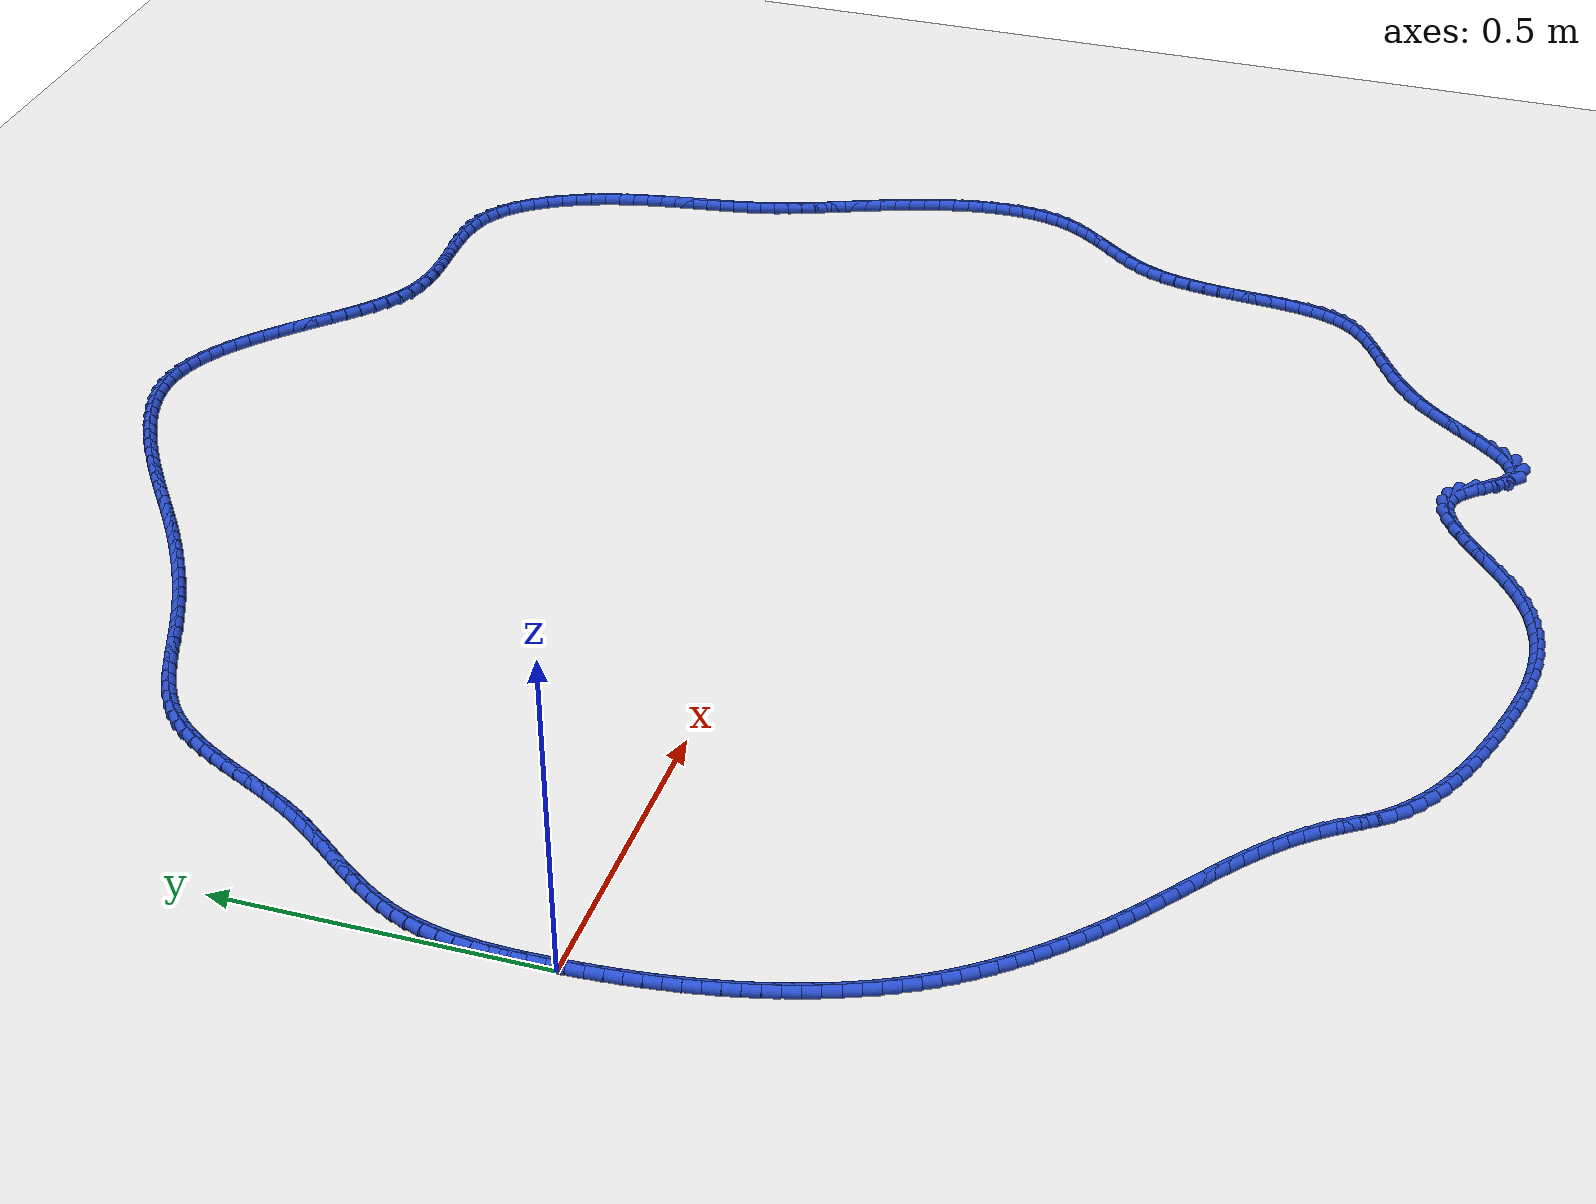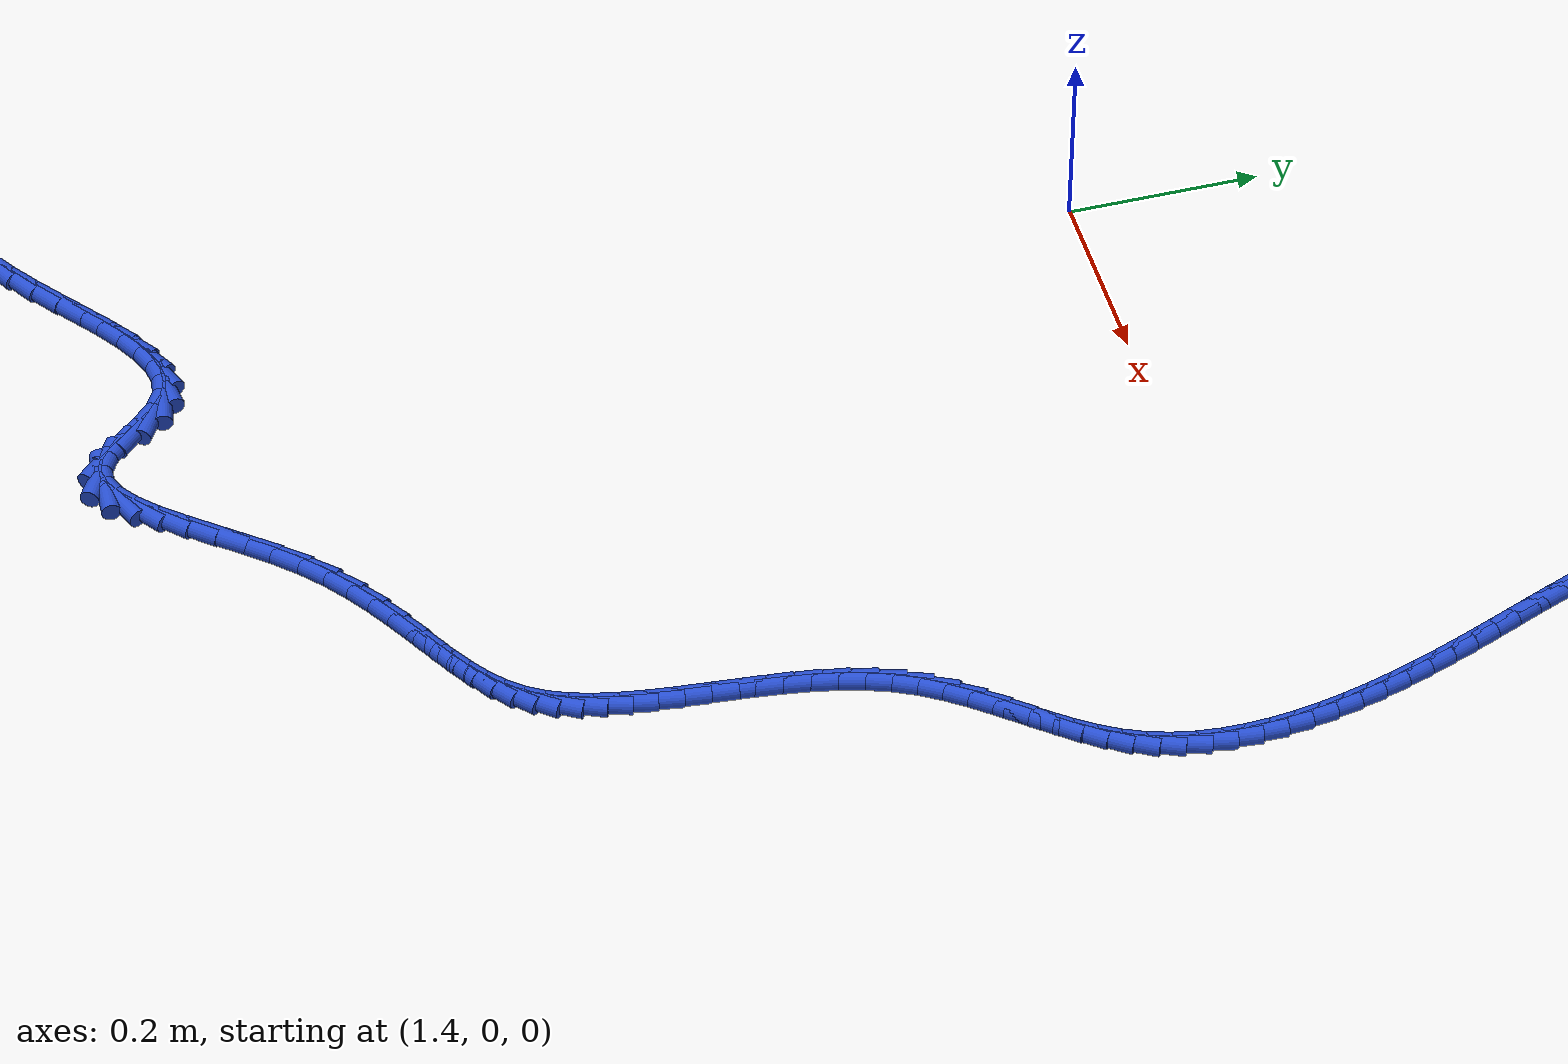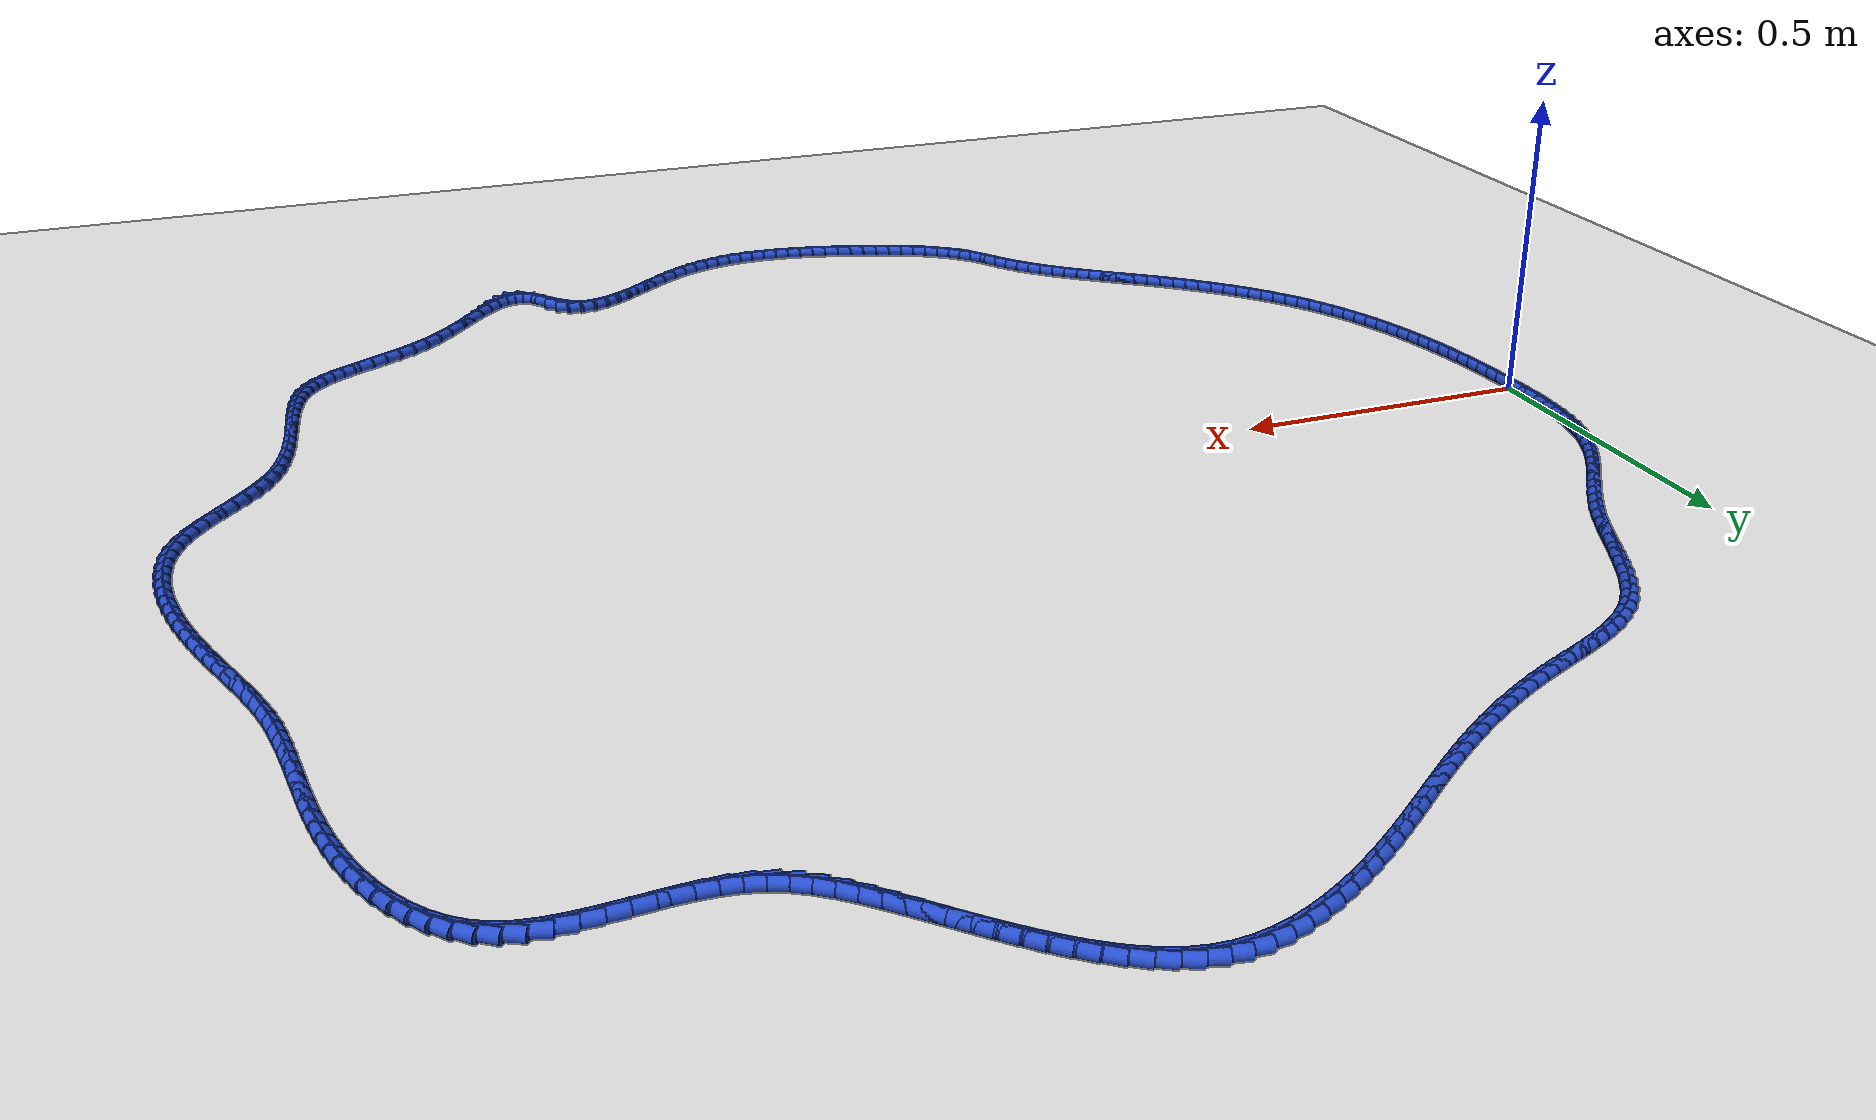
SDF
<sdf version="1.6">
 <world name="default">
  <light name="sun" type="directional">
   <pose>0 0 10 0 -0 0</pose>
   <diffuse>0.8 0.8 0.8 1</diffuse>
   <specular>0.2 0.2 0.2 1</specular>
   <attenuation>
    <range>1000</range>
    <constant>0.9</constant>
    <linear>0.01</linear>
    <quadratic>0.001</quadratic>
   </attenuation>
   <direction>-0.5 0.1 -0.9</direction>
  </light>
  <model name="ground_plane">
   <static>1</static>
   <link name="link">
    <collision name="collision">
     <geometry><plane><normal>0 0 1</normal><size>100 100</size></plane></geometry>
     <surface><friction><ode><mu>100</mu><mu2>50</mu2></ode></friction></surface>
    </collision>
    <visual name="visual">
     <cast_shadows>0</cast_shadows>
     <geometry><plane><normal>0 0 1</normal><size>100 100</size></plane></geometry>
     <material>
      <script><uri>file://media/materials/scripts/gazebo.material</uri><name>Gazebo/WhiteGlow</name></script>
     </material>
    </visual>
   </link>
  </model>
  <gravity>0 0 -9.8</gravity>
  <magnetic_field>6e-06 2.3e-05 -4.2e-05</magnetic_field>
  <atmosphere type="adiabatic"/>
  <physics name="default_physics" default="0" type="ode">
   <max_step_size>0.001</max_step_size>
   <real_time_factor>1</real_time_factor>
   <real_time_update_rate>1000</real_time_update_rate>
  </physics>
  <scene><ambient>0.4 0.4 0.4 1</ambient><background>0.7 0.7 0.7 1</background><shadows>1</shadows></scene>
  <spherical_coordinates>
   <surface_model>EARTH_WGS84</surface_model>
   <latitude_deg>0</latitude_deg>
   <longitude_deg>0</longitude_deg>
   <elevation>0</elevation>
   <heading_deg>0</heading_deg>
  </spherical_coordinates>
  <model name="line">
   <link name="link_0">
    <pose>-9.432558900623889e-18 4.85722573273506e-17 0.01 0 1.57 -1.5440989932306253</pose>
    <collision name="collision">
     <geometry><cylinder><radius>0.01</radius><length>0.08</length></cylinder></geometry>
    </collision>
    <visual name="visual">
     <material>
      <script><name>Gazebo/Blue</name><uri>file://media/materials/scripts/gazebo.material</uri></script>
     </material>
     <geometry><cylinder><radius>0.01</radius><length>0.08</length></cylinder></geometry>
    </visual>
   </link>
   <link name="link_1">
    <pose>-0.0006945769064042888 0.026010533132282784 0.01 0 1.57 -1.5641033546947571</pose>
    <collision name="collision">
     <geometry><cylinder><radius>0.01</radius><length>0.08</length></cylinder></geometry>
    </collision>
    <visual name="visual">
     <material>
      <script><name>Gazebo/Blue</name><uri>file://media/materials/scripts/gazebo.material</uri></script>
     </material>
     <geometry><cylinder><radius>0.01</radius><length>0.08</length></cylinder></geometry>
    </visual>
   </link>
   <link name="link_2">
    <pose>-0.0008692416811515219 0.05210688674604347 0.01 0 1.57 1.551451761372284</pose>
    <collision name="collision">
     <geometry><cylinder><radius>0.01</radius><length>0.08</length></cylinder></geometry>
    </collision>
    <visual name="visual">
     <material>
      <script><name>Gazebo/Blue</name><uri>file://media/materials/scripts/gazebo.material</uri></script>
     </material>
     <geometry><cylinder><radius>0.01</radius><length>0.08</length></cylinder></geometry>
    </visual>
   </link>
   <link name="link_3">
    <pose>-0.0003648800003902909 0.0781761602297236 0.01 0 1.57 1.519067003434756</pose>
    <collision name="collision">
     <geometry><cylinder><radius>0.01</radius><length>0.08</length></cylinder></geometry>
    </collision>
    <visual name="visual">
     <material>
      <script><name>Gazebo/Blue</name><uri>file://media/materials/scripts/gazebo.material</uri></script>
     </material>
     <geometry><cylinder><radius>0.01</radius><length>0.08</length></cylinder></geometry>
    </visual>
   </link>
   <link name="link_4">
    <pose>0.0009776224597308214 0.10410545297176448 0.01 0 1.57 1.4799225139449588</pose>
    <collision name="collision">
     <geometry><cylinder><radius>0.01</radius><length>0.08</length></cylinder></geometry>
    </collision>
    <visual name="visual">
     <material>
      <script><name>Gazebo/Blue</name><uri>file://media/materials/scripts/gazebo.material</uri></script>
     </material>
     <geometry><cylinder><radius>0.01</radius><length>0.08</length></cylinder></geometry>
    </visual>
   </link>
   <link name="link_5">
    <pose>0.003317380023063229 0.12978186436060762 0.01 0 1.57 1.433536079719828</pose>
    <collision name="collision">
     <geometry><cylinder><radius>0.01</radius><length>0.08</length></cylinder></geometry>
    </collision>
    <visual name="visual">
     <material>
      <script><name>Gazebo/Blue</name><uri>file://media/materials/scripts/gazebo.material</uri></script>
     </material>
     <geometry><cylinder><radius>0.01</radius><length>0.08</length></cylinder></geometry>
    </visual>
   </link>
   <link name="link_6">
    <pose>0.006813507013458355 0.15509249378469447 0.01 0 1.57 1.3794011994695092</pose>
    <collision name="collision">
     <geometry><cylinder><radius>0.01</radius><length>0.08</length></cylinder></geometry>
    </collision>
    <visual name="visual">
     <material>
      <script><name>Gazebo/Blue</name><uri>file://media/materials/scripts/gazebo.material</uri></script>
     </material>
     <geometry><cylinder><radius>0.01</radius><length>0.08</length></cylinder></geometry>
    </visual>
   </link>
   <link name="link_7">
    <pose>0.011625117754767612 0.17992444063246638 0.01 0 1.57 1.3170576739655524</pose>
    <collision name="collision">
     <geometry><cylinder><radius>0.01</radius><length>0.08</length></cylinder></geometry>
    </collision>
    <visual name="visual">
     <material>
      <script><name>Gazebo/Blue</name><uri>file://media/materials/scripts/gazebo.material</uri></script>
     </material>
     <geometry><cylinder><radius>0.01</radius><length>0.08</length></cylinder></geometry>
    </visual>
   </link>
   <link name="link_8">
    <pose>0.017911326570842417 0.20416480429236478 0.01 0 1.57 1.2461947583753787</pose>
    <collision name="collision">
     <geometry><cylinder><radius>0.01</radius><length>0.08</length></cylinder></geometry>
    </collision>
    <visual name="visual">
     <material>
      <script><name>Gazebo/Blue</name><uri>file://media/materials/scripts/gazebo.material</uri></script>
     </material>
     <geometry><cylinder><radius>0.01</radius><length>0.08</length></cylinder></geometry>
    </visual>
   </link>
   <link name="link_9">
    <pose>0.025831247785534178 0.2277006841528311 0.01 0 1.57 1.1689381546140352</pose>
    <collision name="collision">
     <geometry><cylinder><radius>0.01</radius><length>0.08</length></cylinder></geometry>
    </collision>
    <visual name="visual">
     <material>
      <script><name>Gazebo/Blue</name><uri>file://media/materials/scripts/gazebo.material</uri></script>
     </material>
     <geometry><cylinder><radius>0.01</radius><length>0.08</length></cylinder></geometry>
    </visual>
   </link>
   <link name="link_10">
    <pose>0.03549824462798571 0.25044734736990293 0.01 0 1.57 1.0984623519737777</pose>
    <collision name="collision">
     <geometry><cylinder><radius>0.01</radius><length>0.08</length></cylinder></geometry>
    </collision>
    <visual name="visual">
     <material>
      <script><name>Gazebo/Blue</name><uri>file://media/materials/scripts/gazebo.material</uri></script>
     </material>
     <geometry><cylinder><radius>0.01</radius><length>0.08</length></cylinder></geometry>
    </visual>
   </link>
   <link name="link_11">
    <pose>0.04675749465776279 0.2724851760911028 0.01 0 1.57 1.0401030312859874</pose>
    <collision name="collision">
     <geometry><cylinder><radius>0.01</radius><length>0.08</length></cylinder></geometry>
    </collision>
    <visual name="visual">
     <material>
      <script><name>Gazebo/Blue</name><uri>file://media/materials/scripts/gazebo.material</uri></script>
     </material>
     <geometry><cylinder><radius>0.01</radius><length>0.08</length></cylinder></geometry>
    </visual>
   </link>
   <link name="link_12">
    <pose>0.05935675718013327 0.293954530367524 0.01 0 1.57 0.9940859030664071</pose>
    <collision name="collision">
     <geometry><cylinder><radius>0.01</radius><length>0.08</length></cylinder></geometry>
    </collision>
    <visual name="visual">
     <material>
      <script><name>Gazebo/Blue</name><uri>file://media/materials/scripts/gazebo.material</uri></script>
     </material>
     <geometry><cylinder><radius>0.01</radius><length>0.08</length></cylinder></geometry>
    </visual>
   </link>
   <link name="link_13">
    <pose>0.07304365355527137 0.3149958551794917 0.01 0 1.57 0.9602471662408425</pose>
    <collision name="collision">
     <geometry><cylinder><radius>0.01</radius><length>0.08</length></cylinder></geometry>
    </collision>
    <visual name="visual">
     <material>
      <script><name>Gazebo/Blue</name><uri>file://media/materials/scripts/gazebo.material</uri></script>
     </material>
     <geometry><cylinder><radius>0.01</radius><length>0.08</length></cylinder></geometry>
    </visual>
   </link>
   <link name="link_14">
    <pose>0.08756580514335131 0.33574959550733097 0.01 0 1.57 0.9382519857669462</pose>
    <collision name="collision">
     <geometry><cylinder><radius>0.01</radius><length>0.08</length></cylinder></geometry>
    </collision>
    <visual name="visual">
     <material>
      <script><name>Gazebo/Blue</name><uri>file://media/materials/scripts/gazebo.material</uri></script>
     </material>
     <geometry><cylinder><radius>0.01</radius><length>0.08</length></cylinder></geometry>
    </visual>
   </link>
   <link name="link_15">
    <pose>0.10267083330454733 0.3563561963313673 0.01 0 1.57 0.9277428616918234</pose>
    <collision name="collision">
     <geometry><cylinder><radius>0.01</radius><length>0.08</length></cylinder></geometry>
    </collision>
    <visual name="visual">
     <material>
      <script><name>Gazebo/Blue</name><uri>file://media/materials/scripts/gazebo.material</uri></script>
     </material>
     <geometry><cylinder><radius>0.01</radius><length>0.08</length></cylinder></geometry>
    </visual>
   </link>
   <link name="link_16">
    <pose>0.11810635939903362 0.3769561026319256 0.01 0 1.57 0.9284258457001995</pose>
    <collision name="collision">
     <geometry><cylinder><radius>0.01</radius><length>0.08</length></cylinder></geometry>
    </collision>
    <visual name="visual">
     <material>
      <script><name>Gazebo/Blue</name><uri>file://media/materials/scripts/gazebo.material</uri></script>
     </material>
     <geometry><cylinder><radius>0.01</radius><length>0.08</length></cylinder></geometry>
    </visual>
   </link>
   <link name="link_17">
    <pose>0.1336200047869845 0.3976897593893314 0.01 0 1.57 0.9401051129426881</pose>
    <collision name="collision">
     <geometry><cylinder><radius>0.01</radius><length>0.08</length></cylinder></geometry>
    </collision>
    <visual name="visual">
     <material>
      <script><name>Gazebo/Blue</name><uri>file://media/materials/scripts/gazebo.material</uri></script>
     </material>
     <geometry><cylinder><radius>0.01</radius><length>0.08</length></cylinder></geometry>
    </visual>
   </link>
   <link name="link_18">
    <pose>0.148959390828574 0.41869761158390956 0.01 0 1.57 0.9626752869535677</pose>
    <collision name="collision">
     <geometry><cylinder><radius>0.01</radius><length>0.08</length></cylinder></geometry>
    </collision>
    <visual name="visual">
     <material>
      <script><name>Gazebo/Blue</name><uri>file://media/materials/scripts/gazebo.material</uri></script>
     </material>
     <geometry><cylinder><radius>0.01</radius><length>0.08</length></cylinder></geometry>
    </visual>
   </link>
   <link name="link_19">
    <pose>0.1638721388839766 0.44012010419598563 0.01 0 1.57 0.9960764072536041</pose>
    <collision name="collision">
     <geometry><cylinder><radius>0.01</radius><length>0.08</length></cylinder></geometry>
    </collision>
    <visual name="visual">
     <material>
      <script><name>Gazebo/Blue</name><uri>file://media/materials/scripts/gazebo.material</uri></script>
     </material>
     <geometry><cylinder><radius>0.01</radius><length>0.08</length></cylinder></geometry>
    </visual>
   </link>
   <link name="link_20">
    <pose>0.1781058703133663 0.46209768220588465 0.01 0 1.57 1.038471397476228</pose>
    <collision name="collision">
     <geometry><cylinder><radius>0.01</radius><length>0.08</length></cylinder></geometry>
    </collision>
    <visual name="visual">
     <material>
      <script><name>Gazebo/Blue</name><uri>file://media/materials/scripts/gazebo.material</uri></script>
     </material>
     <geometry><cylinder><radius>0.01</radius><length>0.08</length></cylinder></geometry>
    </visual>
   </link>
   <link name="link_21">
    <pose>0.1914452358219514 0.4847434565708196 0.01 0 1.57 1.0754194732809101</pose>
    <collision name="collision">
     <geometry><cylinder><radius>0.01</radius><length>0.08</length></cylinder></geometry>
    </collision>
    <visual name="visual">
     <material>
      <script><name>Gazebo/Blue</name><uri>file://media/materials/scripts/gazebo.material</uri></script>
     </material>
     <geometry><cylinder><radius>0.01</radius><length>0.08</length></cylinder></geometry>
    </visual>
   </link>
   <link name="link_22">
    <pose>0.20398109973841444 0.5079444999463887 0.01 0 1.57 1.1000887720050077</pose>
    <collision name="collision">
     <geometry><cylinder><radius>0.01</radius><length>0.08</length></cylinder></geometry>
    </collision>
    <visual name="visual">
     <material>
      <script><name>Gazebo/Blue</name><uri>file://media/materials/scripts/gazebo.material</uri></script>
     </material>
     <geometry><cylinder><radius>0.01</radius><length>0.08</length></cylinder></geometry>
    </visual>
   </link>
   <link name="link_23">
    <pose>0.21595542862052414 0.5314763455640286 0.01 0 1.57 1.1126762225218039</pose>
    <collision name="collision">
     <geometry><cylinder><radius>0.01</radius><length>0.08</length></cylinder></geometry>
    </collision>
    <visual name="visual">
     <material>
      <script><name>Gazebo/Blue</name><uri>file://media/materials/scripts/gazebo.material</uri></script>
     </material>
     <geometry><cylinder><radius>0.01</radius><length>0.08</length></cylinder></geometry>
    </visual>
   </link>
   <link name="link_24">
    <pose>0.2276112545944578 0.5551137400824866 0.01 0 1.57 1.113238810815291</pose>
    <collision name="collision">
     <geometry><cylinder><radius>0.01</radius><length>0.08</length></cylinder></geometry>
    </collision>
    <visual name="visual">
     <material>
      <script><name>Gazebo/Blue</name><uri>file://media/materials/scripts/gazebo.material</uri></script>
     </material>
     <geometry><cylinder><radius>0.01</radius><length>0.08</length></cylinder></geometry>
    </visual>
   </link>
   <link name="link_25">
    <pose>0.23919160978639256 0.57863143016051 0.01 0 1.57 1.101587026631057</pose>
    <collision name="collision">
     <geometry><cylinder><radius>0.01</radius><length>0.08</length></cylinder></geometry>
    </collision>
    <visual name="visual">
     <material>
      <script><name>Gazebo/Blue</name><uri>file://media/materials/scripts/gazebo.material</uri></script>
     </material>
     <geometry><cylinder><radius>0.01</radius><length>0.08</length></cylinder></geometry>
    </visual>
   </link>
   <link name="link_26">
    <pose>0.2509395263225058 0.6018041624568465 0.01 0 1.57 1.077269316741888</pose>
    <collision name="collision">
     <geometry><cylinder><radius>0.01</radius><length>0.08</length></cylinder></geometry>
    </collision>
    <visual name="visual">
     <material>
      <script><name>Gazebo/Blue</name><uri>file://media/materials/scripts/gazebo.material</uri></script>
     </material>
     <geometry><cylinder><radius>0.01</radius><length>0.08</length></cylinder></geometry>
    </visual>
   </link>
   <link name="link_27">
    <pose>0.2630980363289746 0.624406683630243 0.01 0 1.57 1.0396020107929562</pose>
    <collision name="collision">
     <geometry><cylinder><radius>0.01</radius><length>0.08</length></cylinder></geometry>
    </collision>
    <visual name="visual">
     <material>
      <script><name>Gazebo/Blue</name><uri>file://media/materials/scripts/gazebo.material</uri></script>
     </material>
     <geometry><cylinder><radius>0.01</radius><length>0.08</length></cylinder></geometry>
    </visual>
   </link>
   <link name="link_28">
    <pose>0.2759101719319764 0.6462137403394473 0.01 0 1.57 0.9877648865269281</pose>
    <collision name="collision">
     <geometry><cylinder><radius>0.01</radius><length>0.08</length></cylinder></geometry>
    </collision>
    <visual name="visual">
     <material>
      <script><name>Gazebo/Blue</name><uri>file://media/materials/scripts/gazebo.material</uri></script>
     </material>
     <geometry><cylinder><radius>0.01</radius><length>0.08</length></cylinder></geometry>
    </visual>
   </link>
   <link name="link_29">
    <pose>0.2896189652576882 0.6670000792432065 0.01 0 1.57 0.9209971281679276</pose>
    <collision name="collision">
     <geometry><cylinder><radius>0.01</radius><length>0.08</length></cylinder></geometry>
    </collision>
    <visual name="visual">
     <material>
      <script><name>Gazebo/Blue</name><uri>file://media/materials/scripts/gazebo.material</uri></script>
     </material>
     <geometry><cylinder><radius>0.01</radius><length>0.08</length></cylinder></geometry>
    </visual>
   </link>
   <link name="link_30">
    <pose>0.3044674484322874 0.6865404470002678 0.01 0 1.57 0.8389306257135608</pose>
    <collision name="collision">
     <geometry><cylinder><radius>0.01</radius><length>0.08</length></cylinder></geometry>
    </collision>
    <visual name="visual">
     <material>
      <script><name>Gazebo/Blue</name><uri>file://media/materials/scripts/gazebo.material</uri></script>
     </material>
     <geometry><cylinder><radius>0.01</radius><length>0.08</length></cylinder></geometry>
    </visual>
   </link>
   <link name="link_31">
    <pose>0.3206986535819511 0.7046095902693787 0.01 0 1.57 0.7423432842964971</pose>
    <collision name="collision">
     <geometry><cylinder><radius>0.01</radius><length>0.08</length></cylinder></geometry>
    </collision>
    <visual name="visual">
     <material>
      <script><name>Gazebo/Blue</name><uri>file://media/materials/scripts/gazebo.material</uri></script>
     </material>
     <geometry><cylinder><radius>0.01</radius><length>0.08</length></cylinder></geometry>
    </visual>
   </link>
   <link name="link_32">
    <pose>0.33855078986740716 0.7209870635358789 0.01 0 1.57 0.6444809370382992</pose>
    <collision name="collision">
     <geometry><cylinder><radius>0.01</radius><length>0.08</length></cylinder></geometry>
    </collision>
    <visual name="visual">
     <material>
      <script><name>Gazebo/Blue</name><uri>file://media/materials/scripts/gazebo.material</uri></script>
     </material>
     <geometry><cylinder><radius>0.01</radius><length>0.08</length></cylinder></geometry>
    </visual>
   </link>
   <link name="link_33">
    <pose>0.3580628552577548 0.735651007170612 0.01 0 1.57 0.5621185753499015</pose>
    <collision name="collision">
     <geometry><cylinder><radius>0.01</radius><length>0.08</length></cylinder></geometry>
    </collision>
    <visual name="visual">
     <material>
      <script><name>Gazebo/Blue</name><uri>file://media/materials/scripts/gazebo.material</uri></script>
     </material>
     <geometry><cylinder><radius>0.01</radius><length>0.08</length></cylinder></geometry>
    </visual>
   </link>
   <link name="link_34">
    <pose>0.3790080742850786 0.7488445007423732 0.01 0 1.57 0.49627526427810786</pose>
    <collision name="collision">
     <geometry><cylinder><radius>0.01</radius><length>0.08</length></cylinder></geometry>
    </collision>
    <visual name="visual">
     <material>
      <script><name>Gazebo/Blue</name><uri>file://media/materials/scripts/gazebo.material</uri></script>
     </material>
     <geometry><cylinder><radius>0.01</radius><length>0.08</length></cylinder></geometry>
    </visual>
   </link>
   <link name="link_35">
    <pose>0.40114118829294876 0.7608290489913966 0.01 0 1.57 0.44613655816575765</pose>
    <collision name="collision">
     <geometry><cylinder><radius>0.01</radius><length>0.08</length></cylinder></geometry>
    </collision>
    <visual name="visual">
     <material>
      <script><name>Gazebo/Blue</name><uri>file://media/materials/scripts/gazebo.material</uri></script>
     </material>
     <geometry><cylinder><radius>0.01</radius><length>0.08</length></cylinder></geometry>
    </visual>
   </link>
   <link name="link_36">
    <pose>0.42421693862493576 0.7718661566579151 0.01 0 1.57 0.4106589033545149</pose>
    <collision name="collision">
     <geometry><cylinder><radius>0.01</radius><length>0.08</length></cylinder></geometry>
    </collision>
    <visual name="visual">
     <material>
      <script><name>Gazebo/Blue</name><uri>file://media/materials/scripts/gazebo.material</uri></script>
     </material>
     <geometry><cylinder><radius>0.01</radius><length>0.08</length></cylinder></geometry>
    </visual>
   </link>
   <link name="link_37">
    <pose>0.44799006662460955 0.7822173284821623 0.01 0 1.57 0.3888989447708415</pose>
    <collision name="collision">
     <geometry><cylinder><radius>0.01</radius><length>0.08</length></cylinder></geometry>
    </collision>
    <visual name="visual">
     <material>
      <script><name>Gazebo/Blue</name><uri>file://media/materials/scripts/gazebo.material</uri></script>
     </material>
     <geometry><cylinder><radius>0.01</radius><length>0.08</length></cylinder></geometry>
    </visual>
   </link>
   <link name="link_38">
    <pose>0.4722153136355404 0.792144069204372 0.01 0 1.57 0.3801877695011549</pose>
    <collision name="collision">
     <geometry><cylinder><radius>0.01</radius><length>0.08</length></cylinder></geometry>
    </collision>
    <visual name="visual">
     <material>
      <script><name>Gazebo/Blue</name><uri>file://media/materials/scripts/gazebo.material</uri></script>
     </material>
     <geometry><cylinder><radius>0.01</radius><length>0.08</length></cylinder></geometry>
    </visual>
   </link>
   <link name="link_39">
    <pose>0.49664742100129866 0.8019078835647773 0.01 0 1.57 0.38420833800698007</pose>
    <collision name="collision">
     <geometry><cylinder><radius>0.01</radius><length>0.08</length></cylinder></geometry>
    </collision>
    <visual name="visual">
     <material>
      <script><name>Gazebo/Blue</name><uri>file://media/materials/scripts/gazebo.material</uri></script>
     </material>
     <geometry><cylinder><radius>0.01</radius><length>0.08</length></cylinder></geometry>
    </visual>
   </link>
   <link name="link_40">
    <pose>0.5210411300654538 0.8117702763036113 0.01 0 1.57 0.40090159263401615</pose>
    <collision name="collision">
     <geometry><cylinder><radius>0.01</radius><length>0.08</length></cylinder></geometry>
    </collision>
    <visual name="visual">
     <material>
      <script><name>Gazebo/Blue</name><uri>file://media/materials/scripts/gazebo.material</uri></script>
     </material>
     <geometry><cylinder><radius>0.01</radius><length>0.08</length></cylinder></geometry>
    </visual>
   </link>
   <link name="link_41">
    <pose>0.5451533514405603 0.8219903951768729 0.01 0 1.57 0.4250893750855071</pose>
    <collision name="collision">
     <geometry><cylinder><radius>0.01</radius><length>0.08</length></cylinder></geometry>
    </collision>
    <visual name="visual">
     <material>
      <script><name>Gazebo/Blue</name><uri>file://media/materials/scripts/gazebo.material</uri></script>
     </material>
     <geometry><cylinder><radius>0.01</radius><length>0.08</length></cylinder></geometry>
    </visual>
   </link>
   <link name="link_42">
    <pose>0.5688443479538682 0.832715092258177 0.01 0 1.57 0.44906626208551853</pose>
    <collision name="collision">
     <geometry><cylinder><radius>0.01</radius><length>0.08</length></cylinder></geometry>
    </collision>
    <visual name="visual">
     <material>
      <script><name>Gazebo/Blue</name><uri>file://media/materials/scripts/gazebo.material</uri></script>
     </material>
     <geometry><cylinder><radius>0.01</radius><length>0.08</length></cylinder></geometry>
    </visual>
   </link>
   <link name="link_43">
    <pose>0.5921208160401642 0.8439321145460308 0.01 0 1.57 0.4721823302625823</pose>
    <collision name="collision">
     <geometry><cylinder><radius>0.01</radius><length>0.08</length></cylinder></geometry>
    </collision>
    <visual name="visual">
     <material>
      <script><name>Gazebo/Blue</name><uri>file://media/materials/scripts/gazebo.material</uri></script>
     </material>
     <geometry><cylinder><radius>0.01</radius><length>0.08</length></cylinder></geometry>
    </visual>
   </link>
   <link name="link_44">
    <pose>0.6150005669375234 0.8556171324286488 0.01 0 1.57 0.49438379183548414</pose>
    <collision name="collision">
     <geometry><cylinder><radius>0.01</radius><length>0.08</length></cylinder></geometry>
    </collision>
    <visual name="visual">
     <material>
      <script><name>Gazebo/Blue</name><uri>file://media/materials/scripts/gazebo.material</uri></script>
     </material>
     <geometry><cylinder><radius>0.01</radius><length>0.08</length></cylinder></geometry>
    </visual>
   </link>
   <link name="link_45">
    <pose>0.6375014118840205 0.8677458162942455 0.01 0 1.57 0.5156229134149396</pose>
    <collision name="collision">
     <geometry><cylinder><radius>0.01</radius><length>0.08</length></cylinder></geometry>
    </collision>
    <visual name="visual">
     <material>
      <script><name>Gazebo/Blue</name><uri>file://media/materials/scripts/gazebo.material</uri></script>
     </material>
     <geometry><cylinder><radius>0.01</radius><length>0.08</length></cylinder></geometry>
    </visual>
   </link>
   <link name="link_46">
    <pose>0.6596411621177307 0.8802938365310352 0.01 0 1.57 0.5358578727387306</pose>
    <collision name="collision">
     <geometry><cylinder><radius>0.01</radius><length>0.08</length></cylinder></geometry>
    </collision>
    <visual name="visual">
     <material>
      <script><name>Gazebo/Blue</name><uri>file://media/materials/scripts/gazebo.material</uri></script>
     </material>
     <geometry><cylinder><radius>0.01</radius><length>0.08</length></cylinder></geometry>
    </visual>
   </link>
   <link name="link_47">
    <pose>0.6814376288767293 0.8932368635272324 0.01 0 1.57 0.5550524981400397</pose>
    <collision name="collision">
     <geometry><cylinder><radius>0.01</radius><length>0.08</length></cylinder></geometry>
    </collision>
    <visual name="visual">
     <material>
      <script><name>Gazebo/Blue</name><uri>file://media/materials/scripts/gazebo.material</uri></script>
     </material>
     <geometry><cylinder><radius>0.01</radius><length>0.08</length></cylinder></geometry>
    </visual>
   </link>
   <link name="link_48">
    <pose>0.7029086233990909 0.9065505676710512 0.01 0 1.57 0.5731759126766641</pose>
    <collision name="collision">
     <geometry><cylinder><radius>0.01</radius><length>0.08</length></cylinder></geometry>
    </collision>
    <visual name="visual">
     <material>
      <script><name>Gazebo/Blue</name><uri>file://media/materials/scripts/gazebo.material</uri></script>
     </material>
     <geometry><cylinder><radius>0.01</radius><length>0.08</length></cylinder></geometry>
    </visual>
   </link>
   <link name="link_49">
    <pose>0.7240719569228907 0.9202106193507061 0.01 0 1.57 0.5902021052740676</pose>
    <collision name="collision">
     <geometry><cylinder><radius>0.01</radius><length>0.08</length></cylinder></geometry>
    </collision>
    <visual name="visual">
     <material>
      <script><name>Gazebo/Blue</name><uri>file://media/materials/scripts/gazebo.material</uri></script>
     </material>
     <geometry><cylinder><radius>0.01</radius><length>0.08</length></cylinder></geometry>
    </visual>
   </link>
   <link name="link_50">
    <pose>0.7449454406862035 0.9341926889544114 0.01 0 1.57 0.6061026207565823</pose>
    <collision name="collision">
     <geometry><cylinder><radius>0.01</radius><length>0.08</length></cylinder></geometry>
    </collision>
    <visual name="visual">
     <material>
      <script><name>Gazebo/Blue</name><uri>file://media/materials/scripts/gazebo.material</uri></script>
     </material>
     <geometry><cylinder><radius>0.01</radius><length>0.08</length></cylinder></geometry>
    </visual>
   </link>
   <link name="link_51">
    <pose>0.7655470463820114 0.9484723497857341 0.01 0 1.57 0.6197247595487537</pose>
    <collision name="collision">
     <geometry><cylinder><radius>0.01</radius><length>0.08</length></cylinder></geometry>
    </collision>
    <visual name="visual">
     <material>
      <script><name>Gazebo/Blue</name><uri>file://media/materials/scripts/gazebo.material</uri></script>
     </material>
     <geometry><cylinder><radius>0.01</radius><length>0.08</length></cylinder></geometry>
    </visual>
   </link>
   <link name="link_52">
    <pose>0.7859211934904183 0.9630091726829545 0.01 0 1.57 0.6286331147928967</pose>
    <collision name="collision">
     <geometry><cylinder><radius>0.01</radius><length>0.08</length></cylinder></geometry>
    </collision>
    <visual name="visual">
     <material>
      <script><name>Gazebo/Blue</name><uri>file://media/materials/scripts/gazebo.material</uri></script>
     </material>
     <geometry><cylinder><radius>0.01</radius><length>0.08</length></cylinder></geometry>
    </visual>
   </link>
   <link name="link_53">
    <pose>0.8061679664141729 0.9777290479352668 0.01 0 1.57 0.6324843587315332</pose>
    <collision name="collision">
     <geometry><cylinder><radius>0.01</radius><length>0.08</length></cylinder></geometry>
    </collision>
    <visual name="visual">
     <material>
      <script><name>Gazebo/Blue</name><uri>file://media/materials/scripts/gazebo.material</uri></script>
     </material>
     <geometry><cylinder><radius>0.01</radius><length>0.08</length></cylinder></geometry>
    </visual>
   </link>
   <link name="link_54">
    <pose>0.8263944890279851 0.9925536065376879 0.01 0 1.57 0.6312869231386798</pose>
    <collision name="collision">
     <geometry><cylinder><radius>0.01</radius><length>0.08</length></cylinder></geometry>
    </collision>
    <visual name="visual">
     <material>
      <script><name>Gazebo/Blue</name><uri>file://media/materials/scripts/gazebo.material</uri></script>
     </material>
     <geometry><cylinder><radius>0.01</radius><length>0.08</length></cylinder></geometry>
    </visual>
   </link>
   <link name="link_55">
    <pose>0.8467078852065647 1.0074044794852337 0.01 0 1.57 0.6250978969013516</pose>
    <collision name="collision">
     <geometry><cylinder><radius>0.01</radius><length>0.08</length></cylinder></geometry>
    </collision>
    <visual name="visual">
     <material>
      <script><name>Gazebo/Blue</name><uri>file://media/materials/scripts/gazebo.material</uri></script>
     </material>
     <geometry><cylinder><radius>0.01</radius><length>0.08</length></cylinder></geometry>
    </visual>
   </link>
   <link name="link_56">
    <pose>0.8672152788246221 1.0222032977729214 0.01 0 1.57 0.6140221579124837</pose>
    <collision name="collision">
     <geometry><cylinder><radius>0.01</radius><length>0.08</length></cylinder></geometry>
    </collision>
    <visual name="visual">
     <material>
      <script><name>Gazebo/Blue</name><uri>file://media/materials/scripts/gazebo.material</uri></script>
     </material>
     <geometry><cylinder><radius>0.01</radius><length>0.08</length></cylinder></geometry>
    </visual>
   </link>
   <link name="link_57">
    <pose>0.8880237937568672 1.0368716923957675 0.01 0 1.57 0.5982138817994356</pose>
    <collision name="collision">
     <geometry><cylinder><radius>0.01</radius><length>0.08</length></cylinder></geometry>
    </collision>
    <visual name="visual">
     <material>
      <script><name>Gazebo/Blue</name><uri>file://media/materials/scripts/gazebo.material</uri></script>
     </material>
     <geometry><cylinder><radius>0.01</radius><length>0.08</length></cylinder></geometry>
    </visual>
   </link>
   <link name="link_58">
    <pose>0.9092405538780102 1.0513312943487885 0.01 0 1.57 0.5778797432441662</pose>
    <collision name="collision">
     <geometry><cylinder><radius>0.01</radius><length>0.08</length></cylinder></geometry>
    </collision>
    <visual name="visual">
     <material>
      <script><name>Gazebo/Blue</name><uri>file://media/materials/scripts/gazebo.material</uri></script>
     </material>
     <geometry><cylinder><radius>0.01</radius><length>0.08</length></cylinder></geometry>
    </visual>
   </link>
   <link name="link_59">
    <pose>0.9309726830627609 1.0655037346270009 0.01 0 1.57 0.553282765120305</pose>
    <collision name="collision">
     <geometry><cylinder><radius>0.01</radius><length>0.08</length></cylinder></geometry>
    </collision>
    <visual name="visual">
     <material>
      <script><name>Gazebo/Blue</name><uri>file://media/materials/scripts/gazebo.material</uri></script>
     </material>
     <geometry><cylinder><radius>0.01</radius><length>0.08</length></cylinder></geometry>
    </visual>
   </link>
   <link name="link_60">
    <pose>0.9533273051858295 1.0793106442254214 0.01 0 1.57 0.5244381603737651</pose>
    <collision name="collision">
     <geometry><cylinder><radius>0.01</radius><length>0.08</length></cylinder></geometry>
    </collision>
    <visual name="visual">
     <material>
      <script><name>Gazebo/Blue</name><uri>file://media/materials/scripts/gazebo.material</uri></script>
     </material>
     <geometry><cylinder><radius>0.01</radius><length>0.08</length></cylinder></geometry>
    </visual>
   </link>
   <link name="link_61">
    <pose>0.9763883771816332 1.092650782353551 0.01 0 1.57 0.4891227898524606</pose>
    <collision name="collision">
     <geometry><cylinder><radius>0.01</radius><length>0.08</length></cylinder></geometry>
    </collision>
    <visual name="visual">
     <material>
      <script><name>Gazebo/Blue</name><uri>file://media/materials/scripts/gazebo.material</uri></script>
     </material>
     <geometry><cylinder><radius>0.01</radius><length>0.08</length></cylinder></geometry>
    </visual>
   </link>
   <link name="link_62">
    <pose>1.0000708604780975 1.1052560657751973 0.01 0 1.57 0.4454749804757394</pose>
    <collision name="collision">
     <geometry><cylinder><radius>0.01</radius><length>0.08</length></cylinder></geometry>
    </collision>
    <visual name="visual">
     <material>
      <script><name>Gazebo/Blue</name><uri>file://media/materials/scripts/gazebo.material</uri></script>
     </material>
     <geometry><cylinder><radius>0.01</radius><length>0.08</length></cylinder></geometry>
    </visual>
   </link>
   <link name="link_63">
    <pose>1.0242148332927983 1.1167844820816408 0.01 0 1.57 0.3921287623526055</pose>
    <collision name="collision">
     <geometry><cylinder><radius>0.01</radius><length>0.08</length></cylinder></geometry>
    </collision>
    <visual name="visual">
     <material>
      <script><name>Gazebo/Blue</name><uri>file://media/materials/scripts/gazebo.material</uri></script>
     </material>
     <geometry><cylinder><radius>0.01</radius><length>0.08</length></cylinder></geometry>
    </visual>
   </link>
   <link name="link_64">
    <pose>1.0486600386861396 1.1268936879770057 0.01 0 1.57 0.32731372559247807</pose>
    <collision name="collision">
     <geometry><cylinder><radius>0.01</radius><length>0.08</length></cylinder></geometry>
    </collision>
    <visual name="visual">
     <material>
      <script><name>Gazebo/Blue</name><uri>file://media/materials/scripts/gazebo.material</uri></script>
     </material>
     <geometry><cylinder><radius>0.01</radius><length>0.08</length></cylinder></geometry>
    </visual>
   </link>
   <link name="link_65">
    <pose>1.0732462197185249 1.135241340165418 0.01 0 1.57 0.24888368320304344</pose>
    <collision name="collision">
     <geometry><cylinder><radius>0.01</radius><length>0.08</length></cylinder></geometry>
    </collision>
    <visual name="visual">
     <material>
      <script><name>Gazebo/Blue</name><uri>file://media/materials/scripts/gazebo.material</uri></script>
     </material>
     <geometry><cylinder><radius>0.01</radius><length>0.08</length></cylinder></geometry>
    </visual>
   </link>
   <link name="link_66">
    <pose>1.097813119450359 1.141485095351003 0.01 0 1.57 0.15447592653696843</pose>
    <collision name="collision">
     <geometry><cylinder><radius>0.01</radius><length>0.08</length></cylinder></geometry>
    </collision>
    <visual name="visual">
     <material>
      <script><name>Gazebo/Blue</name><uri>file://media/materials/scripts/gazebo.material</uri></script>
     </material>
     <geometry><cylinder><radius>0.01</radius><length>0.08</length></cylinder></geometry>
    </visual>
   </link>
   <link name="link_67">
    <pose>1.1222004809420456 1.1452826102378861 0.01 0 1.57 0.04193105881487186</pose>
    <collision name="collision">
     <geometry><cylinder><radius>0.01</radius><length>0.08</length></cylinder></geometry>
    </collision>
    <visual name="visual">
     <material>
      <script><name>Gazebo/Blue</name><uri>file://media/materials/scripts/gazebo.material</uri></script>
     </material>
     <geometry><cylinder><radius>0.01</radius><length>0.08</length></cylinder></geometry>
    </visual>
   </link>
   <link name="link_68">
    <pose>1.1462480472539893 1.1462915415301924 0.01 0 1.57 -0.08743163700824086</pose>
    <collision name="collision">
     <geometry><cylinder><radius>0.01</radius><length>0.08</length></cylinder></geometry>
    </collision>
    <visual name="visual">
     <material>
      <script><name>Gazebo/Blue</name><uri>file://media/materials/scripts/gazebo.material</uri></script>
     </material>
     <geometry><cylinder><radius>0.01</radius><length>0.08</length></cylinder></geometry>
    </visual>
   </link>
   <link name="link_69">
    <pose>1.1698132841623476 1.1442259282233576 0.01 0 1.57 -0.21465080903056108</pose>
    <collision name="collision">
     <geometry><cylinder><radius>0.01</radius><length>0.08</length></cylinder></geometry>
    </collision>
    <visual name="visual">
     <material>
      <script><name>Gazebo/Blue</name><uri>file://media/materials/scripts/gazebo.material</uri></script>
     </material>
     <geometry><cylinder><radius>0.01</radius><length>0.08</length></cylinder></geometry>
    </visual>
   </link>
   <link name="link_70">
    <pose>1.192878651884994 1.139197461293627 0.01 0 1.57 -0.3286902507180366</pose>
    <collision name="collision">
     <geometry><cylinder><radius>0.01</radius><length>0.08</length></cylinder></geometry>
    </collision>
    <visual name="visual">
     <material>
      <script><name>Gazebo/Blue</name><uri>file://media/materials/scripts/gazebo.material</uri></script>
     </material>
     <geometry><cylinder><radius>0.01</radius><length>0.08</length></cylinder></geometry>
    </visual>
   </link>
   <link name="link_71">
    <pose>1.2154803734587398 1.1314888704542576 0.01 0 1.57 -0.4275987860805969</pose>
    <collision name="collision">
     <geometry><cylinder><radius>0.01</radius><length>0.08</length></cylinder></geometry>
    </collision>
    <visual name="visual">
     <material>
      <script><name>Gazebo/Blue</name><uri>file://media/materials/scripts/gazebo.material</uri></script>
     </material>
     <geometry><cylinder><radius>0.01</radius><length>0.08</length></cylinder></geometry>
    </visual>
   </link>
   <link name="link_72">
    <pose>1.2376548806841392 1.1213835495705664 0.01 0 1.57 -0.5111789919671377</pose>
    <collision name="collision">
     <geometry><cylinder><radius>0.01</radius><length>0.08</length></cylinder></geometry>
    </collision>
    <visual name="visual">
     <material>
      <script><name>Gazebo/Blue</name><uri>file://media/materials/scripts/gazebo.material</uri></script>
     </material>
     <geometry><cylinder><radius>0.01</radius><length>0.08</length></cylinder></geometry>
    </visual>
   </link>
   <link name="link_73">
    <pose>1.2594386053617455 1.1091648925078692 0.01 0 1.57 -0.5802856245420731</pose>
    <collision name="collision">
     <geometry><cylinder><radius>0.01</radius><length>0.08</length></cylinder></geometry>
    </collision>
    <visual name="visual">
     <material>
      <script><name>Gazebo/Blue</name><uri>file://media/materials/scripts/gazebo.material</uri></script>
     </material>
     <geometry><cylinder><radius>0.01</radius><length>0.08</length></cylinder></geometry>
    </visual>
   </link>
   <link name="link_74">
    <pose>1.2808679792921134 1.0951162931314842 0.01 0 1.57 -0.6362333523583795</pose>
    <collision name="collision">
     <geometry><cylinder><radius>0.01</radius><length>0.08</length></cylinder></geometry>
    </collision>
    <visual name="visual">
     <material>
      <script><name>Gazebo/Blue</name><uri>file://media/materials/scripts/gazebo.material</uri></script>
     </material>
     <geometry><cylinder><radius>0.01</radius><length>0.08</length></cylinder></geometry>
    </visual>
   </link>
   <link name="link_75">
    <pose>1.3019794342757969 1.079521145306728 0.01 0 1.57 -0.6804036828599782</pose>
    <collision name="collision">
     <geometry><cylinder><radius>0.01</radius><length>0.08</length></cylinder></geometry>
    </collision>
    <visual name="visual">
     <material>
      <script><name>Gazebo/Blue</name><uri>file://media/materials/scripts/gazebo.material</uri></script>
     </material>
     <geometry><cylinder><radius>0.01</radius><length>0.08</length></cylinder></geometry>
    </visual>
   </link>
   <link name="link_76">
    <pose>1.3228094021133503 1.0626628428989173 0.01 0 1.57 -0.7140298193267032</pose>
    <collision name="collision">
     <geometry><cylinder><radius>0.01</radius><length>0.08</length></cylinder></geometry>
    </collision>
    <visual name="visual">
     <material>
      <script><name>Gazebo/Blue</name><uri>file://media/materials/scripts/gazebo.material</uri></script>
     </material>
     <geometry><cylinder><radius>0.01</radius><length>0.08</length></cylinder></geometry>
    </visual>
   </link>
   <link name="link_77">
    <pose>1.343394314605327 1.0448247797733692 0.01 0 1.57 -0.738097953793061</pose>
    <collision name="collision">
     <geometry><cylinder><radius>0.01</radius><length>0.08</length></cylinder></geometry>
    </collision>
    <visual name="visual">
     <material>
      <script><name>Gazebo/Blue</name><uri>file://media/materials/scripts/gazebo.material</uri></script>
     </material>
     <geometry><cylinder><radius>0.01</radius><length>0.08</length></cylinder></geometry>
    </visual>
   </link>
   <link name="link_78">
    <pose>1.3637706035522816 1.026290349795401 0.01 0 1.57 -0.7533109404504127</pose>
    <collision name="collision">
     <geometry><cylinder><radius>0.01</radius><length>0.08</length></cylinder></geometry>
    </collision>
    <visual name="visual">
     <material>
      <script><name>Gazebo/Blue</name><uri>file://media/materials/scripts/gazebo.material</uri></script>
     </material>
     <geometry><cylinder><radius>0.01</radius><length>0.08</length></cylinder></geometry>
    </visual>
   </link>
   <link name="link_79">
    <pose>1.3839747007547687 1.0073429468303294 0.01 0 1.57 -0.7600785764646717</pose>
    <collision name="collision">
     <geometry><cylinder><radius>0.01</radius><length>0.08</length></cylinder></geometry>
    </collision>
    <visual name="visual">
     <material>
      <script><name>Gazebo/Blue</name><uri>file://media/materials/scripts/gazebo.material</uri></script>
     </material>
     <geometry><cylinder><radius>0.01</radius><length>0.08</length></cylinder></geometry>
    </visual>
   </link>
   <link name="link_80">
    <pose>1.4040430380133404 0.9882659647434713 0.01 0 1.57 -0.7585138414490824</pose>
    <collision name="collision">
     <geometry><cylinder><radius>0.01</radius><length>0.08</length></cylinder></geometry>
    </collision>
    <visual name="visual">
     <material>
      <script><name>Gazebo/Blue</name><uri>file://media/materials/scripts/gazebo.material</uri></script>
     </material>
     <geometry><cylinder><radius>0.01</radius><length>0.08</length></cylinder></geometry>
    </visual>
   </link>
   <link name="link_81">
    <pose>1.4240120471285527 0.9693427974001434 0.01 0 1.57 -0.7479501904818517</pose>
    <collision name="collision">
     <geometry><cylinder><radius>0.01</radius><length>0.08</length></cylinder></geometry>
    </collision>
    <visual name="visual">
     <material>
      <script><name>Gazebo/Blue</name><uri>file://media/materials/scripts/gazebo.material</uri></script>
     </material>
     <geometry><cylinder><radius>0.01</radius><length>0.08</length></cylinder></geometry>
    </visual>
   </link>
   <link name="link_82">
    <pose>1.443927523505029 0.9508657168952637 0.01 0 1.57 -0.7223153956248793</pose>
    <collision name="collision">
     <geometry><cylinder><radius>0.01</radius><length>0.08</length></cylinder></geometry>
    </collision>
    <visual name="visual">
     <material>
      <script><name>Gazebo/Blue</name><uri>file://media/materials/scripts/gazebo.material</uri></script>
     </material>
     <geometry><cylinder><radius>0.01</radius><length>0.08</length></cylinder></geometry>
    </visual>
   </link>
   <link name="link_83">
    <pose>1.4639427137284262 0.9332288766345065 0.01 0 1.57 -0.6767731738078261</pose>
    <collision name="collision">
     <geometry><cylinder><radius>0.01</radius><length>0.08</length></cylinder></geometry>
    </collision>
    <visual name="visual">
     <material>
      <script><name>Gazebo/Blue</name><uri>file://media/materials/scripts/gazebo.material</uri></script>
     </material>
     <geometry><cylinder><radius>0.01</radius><length>0.08</length></cylinder></geometry>
    </visual>
   </link>
   <link name="link_84">
    <pose>1.4842795283573547 0.916891534711082 0.01 0 1.57 -0.6094553774091954</pose>
    <collision name="collision">
     <geometry><cylinder><radius>0.01</radius><length>0.08</length></cylinder></geometry>
    </collision>
    <visual name="visual">
     <material>
      <script><name>Gazebo/Blue</name><uri>file://media/materials/scripts/gazebo.material</uri></script>
     </material>
     <geometry><cylinder><radius>0.01</radius><length>0.08</length></cylinder></geometry>
    </visual>
   </link>
   <link name="link_85">
    <pose>1.5051609930874839 0.9023140065506928 0.01 0 1.57 -0.5186745632117382</pose>
    <collision name="collision">
     <geometry><cylinder><radius>0.01</radius><length>0.08</length></cylinder></geometry>
    </collision>
    <visual name="visual">
     <material>
      <script><name>Gazebo/Blue</name><uri>file://media/materials/scripts/gazebo.material</uri></script>
     </material>
     <geometry><cylinder><radius>0.01</radius><length>0.08</length></cylinder></geometry>
    </visual>
   </link>
   <link name="link_86">
    <pose>1.526810133614482 0.8899566075790422 0.01 0 1.57 -0.4039273271296346</pose>
    <collision name="collision">
     <geometry><cylinder><radius>0.01</radius><length>0.08</length></cylinder></geometry>
    </collision>
    <visual name="visual">
     <material>
      <script><name>Gazebo/Blue</name><uri>file://media/materials/scripts/gazebo.material</uri></script>
     </material>
     <geometry><cylinder><radius>0.01</radius><length>0.08</length></cylinder></geometry>
    </visual>
   </link>
   <link name="link_87">
    <pose>1.5494499756340188 0.8802796532218333 0.01 0 1.57 -0.2695141866518195</pose>
    <collision name="collision">
     <geometry><cylinder><radius>0.01</radius><length>0.08</length></cylinder></geometry>
    </collision>
    <visual name="visual">
     <material>
      <script><name>Gazebo/Blue</name><uri>file://media/materials/scripts/gazebo.material</uri></script>
     </material>
     <geometry><cylinder><radius>0.01</radius><length>0.08</length></cylinder></geometry>
    </visual>
   </link>
   <link name="link_88">
    <pose>1.5732826852961739 0.8736962203333054 0.01 0 1.57 -0.14713887892566568</pose>
    <collision name="collision">
     <geometry><cylinder><radius>0.01</radius><length>0.08</length></cylinder></geometry>
    </collision>
    <visual name="visual">
     <material>
      <script><name>Gazebo/Blue</name><uri>file://media/materials/scripts/gazebo.material</uri></script>
     </material>
     <geometry><cylinder><radius>0.01</radius><length>0.08</length></cylinder></geometry>
    </visual>
   </link>
   <link name="link_89">
    <pose>1.5982359899344063 0.8699978910378251 0.01 0 1.57 -0.056506062015166045</pose>
    <collision name="collision">
     <geometry><cylinder><radius>0.01</radius><length>0.08</length></cylinder></geometry>
    </collision>
    <visual name="visual">
     <material>
      <script><name>Gazebo/Blue</name><uri>file://media/materials/scripts/gazebo.material</uri></script>
     </material>
     <geometry><cylinder><radius>0.01</radius><length>0.08</length></cylinder></geometry>
    </visual>
   </link>
   <link name="link_90">
    <pose>1.6240441058455097 0.8685380219531007 0.01 0 1.57 0.0046516184004331594</pose>
    <collision name="collision">
     <geometry><cylinder><radius>0.01</radius><length>0.08</length></cylinder></geometry>
    </collision>
    <visual name="visual">
     <material>
      <script><name>Gazebo/Blue</name><uri>file://media/materials/scripts/gazebo.material</uri></script>
     </material>
     <geometry><cylinder><radius>0.01</radius><length>0.08</length></cylinder></geometry>
    </visual>
   </link>
   <link name="link_91">
    <pose>1.650437197281841 0.868660793428363 0.01 0 1.57 0.03927824934825642</pose>
    <collision name="collision">
     <geometry><cylinder><radius>0.01</radius><length>0.08</length></cylinder></geometry>
    </collision>
    <visual name="visual">
     <material>
      <script><name>Gazebo/Blue</name><uri>file://media/materials/scripts/gazebo.material</uri></script>
     </material>
     <geometry><cylinder><radius>0.01</radius><length>0.08</length></cylinder></geometry>
    </visual>
   </link>
   <link name="link_92">
    <pose>1.6771454284957583 0.8697103858128428 0.01 0 1.57 0.04932143099108213</pose>
    <collision name="collision">
     <geometry><cylinder><radius>0.01</radius><length>0.08</length></cylinder></geometry>
    </collision>
    <visual name="visual">
     <material>
      <script><name>Gazebo/Blue</name><uri>file://media/materials/scripts/gazebo.material</uri></script>
     </material>
     <geometry><cylinder><radius>0.01</radius><length>0.08</length></cylinder></geometry>
    </visual>
   </link>
   <link name="link_93">
    <pose>1.7038989637396191 0.8710309794557706 0.01 0 1.57 0.03525904891644092</pose>
    <collision name="collision">
     <geometry><cylinder><radius>0.01</radius><length>0.08</length></cylinder></geometry>
    </collision>
    <visual name="visual">
     <material>
      <script><name>Gazebo/Blue</name><uri>file://media/materials/scripts/gazebo.material</uri></script>
     </material>
     <geometry><cylinder><radius>0.01</radius><length>0.08</length></cylinder></geometry>
    </visual>
   </link>
   <link name="link_94">
    <pose>1.730427967265781 0.8719667547063767 0.01 0 1.57 -0.004027796861501144</pose>
    <collision name="collision">
     <geometry><cylinder><radius>0.01</radius><length>0.08</length></cylinder></geometry>
    </collision>
    <visual name="visual">
     <material>
      <script><name>Gazebo/Blue</name><uri>file://media/materials/scripts/gazebo.material</uri></script>
     </material>
     <geometry><cylinder><radius>0.01</radius><length>0.08</length></cylinder></geometry>
    </visual>
   </link>
   <link name="link_95">
    <pose>1.756462603326601 0.8718618919138919 0.01 0 1.57 -0.07116137962731606</pose>
    <collision name="collision">
     <geometry><cylinder><radius>0.01</radius><length>0.08</length></cylinder></geometry>
    </collision>
    <visual name="visual">
     <material>
      <script><name>Gazebo/Blue</name><uri>file://media/materials/scripts/gazebo.material</uri></script>
     </material>
     <geometry><cylinder><radius>0.01</radius><length>0.08</length></cylinder></geometry>
    </visual>
   </link>
   <link name="link_96">
    <pose>1.7817330361744361 0.8700605714275467 0.01 0 1.57 -0.16972967174207992</pose>
    <collision name="collision">
     <geometry><cylinder><radius>0.01</radius><length>0.08</length></cylinder></geometry>
    </collision>
    <visual name="visual">
     <material>
      <script><name>Gazebo/Blue</name><uri>file://media/materials/scripts/gazebo.material</uri></script>
     </material>
     <geometry><cylinder><radius>0.01</radius><length>0.08</length></cylinder></geometry>
    </visual>
   </link>
   <link name="link_97">
    <pose>1.8059694300616447 0.8659069735965715 0.01 0 1.57 -0.30269745025292033</pose>
    <collision name="collision">
     <geometry><cylinder><radius>0.01</radius><length>0.08</length></cylinder></geometry>
    </collision>
    <visual name="visual">
     <material>
      <script><name>Gazebo/Blue</name><uri>file://media/materials/scripts/gazebo.material</uri></script>
     </material>
     <geometry><cylinder><radius>0.01</radius><length>0.08</length></cylinder></geometry>
    </visual>
   </link>
   <link name="link_98">
    <pose>1.8289019492405845 0.8587452787701975 0.01 0 1.57 -0.46677637265455685</pose>
    <collision name="collision">
     <geometry><cylinder><radius>0.01</radius><length>0.08</length></cylinder></geometry>
    </collision>
    <visual name="visual">
     <material>
      <script><name>Gazebo/Blue</name><uri>file://media/materials/scripts/gazebo.material</uri></script>
     </material>
     <geometry><cylinder><radius>0.01</radius><length>0.08</length></cylinder></geometry>
    </visual>
   </link>
   <link name="link_99">
    <pose>1.850274858227614 0.847975104557877 0.01 0 1.57 -0.6279419408262584</pose>
    <collision name="collision">
     <geometry><cylinder><radius>0.01</radius><length>0.08</length></cylinder></geometry>
    </collision>
    <visual name="visual">
     <material>
      <script><name>Gazebo/Blue</name><uri>file://media/materials/scripts/gazebo.material</uri></script>
     </material>
     <geometry><cylinder><radius>0.01</radius><length>0.08</length></cylinder></geometry>
    </visual>
   </link>
   <link name="link_100">
    <pose>1.8700000791358273 0.8336552390510531 0.01 0 1.57 -0.7650778649873952</pose>
    <collision name="collision">
     <geometry><cylinder><radius>0.01</radius><length>0.08</length></cylinder></geometry>
    </collision>
    <visual name="visual">
     <material>
      <script><name>Gazebo/Blue</name><uri>file://media/materials/scripts/gazebo.material</uri></script>
     </material>
     <geometry><cylinder><radius>0.01</radius><length>0.08</length></cylinder></geometry>
    </visual>
   </link>
   <link name="link_101">
    <pose>1.8880995040571078 0.8162768334749403 0.01 0 1.57 -0.8795545050842294</pose>
    <collision name="collision">
     <geometry><cylinder><radius>0.01</radius><length>0.08</length></cylinder></geometry>
    </collision>
    <visual name="visual">
     <material>
      <script><name>Gazebo/Blue</name><uri>file://media/materials/scripts/gazebo.material</uri></script>
     </material>
     <geometry><cylinder><radius>0.01</radius><length>0.08</length></cylinder></geometry>
    </visual>
   </link>
   <link name="link_102">
    <pose>1.9045969406870047 0.796338570532093 0.01 0 1.57 -0.9748752949427961</pose>
    <collision name="collision">
     <geometry><cylinder><radius>0.01</radius><length>0.08</length></cylinder></geometry>
    </collision>
    <visual name="visual">
     <material>
      <script><name>Gazebo/Blue</name><uri>file://media/materials/scripts/gazebo.material</uri></script>
     </material>
     <geometry><cylinder><radius>0.01</radius><length>0.08</length></cylinder></geometry>
    </visual>
   </link>
   <link name="link_103">
    <pose>1.9195161967210668 0.774339132925064 0.01 0 1.57 -1.0548258357660034</pose>
    <collision name="collision">
     <geometry><cylinder><radius>0.01</radius><length>0.08</length></cylinder></geometry>
    </collision>
    <visual name="visual">
     <material>
      <script><name>Gazebo/Blue</name><uri>file://media/materials/scripts/gazebo.material</uri></script>
     </material>
     <geometry><cylinder><radius>0.01</radius><length>0.08</length></cylinder></geometry>
    </visual>
   </link>
   <link name="link_104">
    <pose>1.9328810798548424 0.7507772033564072 0.01 0 1.57 -1.122815611410617</pose>
    <collision name="collision">
     <geometry><cylinder><radius>0.01</radius><length>0.08</length></cylinder></geometry>
    </collision>
    <visual name="visual">
     <material>
      <script><name>Gazebo/Blue</name><uri>file://media/materials/scripts/gazebo.material</uri></script>
     </material>
     <geometry><cylinder><radius>0.01</radius><length>0.08</length></cylinder></geometry>
    </visual>
   </link>
   <link name="link_105">
    <pose>1.94471539778388 0.7261514645286763 0.01 0 1.57 -1.1817226941694174</pose>
    <collision name="collision">
     <geometry><cylinder><radius>0.01</radius><length>0.08</length></cylinder></geometry>
    </collision>
    <visual name="visual">
     <material>
      <script><name>Gazebo/Blue</name><uri>file://media/materials/scripts/gazebo.material</uri></script>
     </material>
     <geometry><cylinder><radius>0.01</radius><length>0.08</length></cylinder></geometry>
    </visual>
   </link>
   <link name="link_106">
    <pose>1.9550429582037288 0.7009605991444248 0.01 0 1.57 -1.2339732360330775</pose>
    <collision name="collision">
     <geometry><cylinder><radius>0.01</radius><length>0.08</length></cylinder></geometry>
    </collision>
    <visual name="visual">
     <material>
      <script><name>Gazebo/Blue</name><uri>file://media/materials/scripts/gazebo.material</uri></script>
     </material>
     <geometry><cylinder><radius>0.01</radius><length>0.08</length></cylinder></geometry>
    </visual>
   </link>
   <link name="link_107">
    <pose>1.9639114246876614 0.6756341675154082 0.01 0 1.57 -1.2807311738087934</pose>
    <collision name="collision">
     <geometry><cylinder><radius>0.01</radius><length>0.08</length></cylinder></geometry>
    </collision>
    <visual name="visual">
     <material>
      <script><name>Gazebo/Blue</name><uri>file://media/materials/scripts/gazebo.material</uri></script>
     </material>
     <geometry><cylinder><radius>0.01</radius><length>0.08</length></cylinder></geometry>
    </visual>
   </link>
   <link name="link_108">
    <pose>1.9714775265768874 0.6502857119589476 0.01 0 1.57 -1.3215588655272386</pose>
    <collision name="collision">
     <geometry><cylinder><radius>0.01</radius><length>0.08</length></cylinder></geometry>
    </collision>
    <visual name="visual">
     <material>
      <script><name>Gazebo/Blue</name><uri>file://media/materials/scripts/gazebo.material</uri></script>
     </material>
     <geometry><cylinder><radius>0.01</radius><length>0.08</length></cylinder></geometry>
    </visual>
   </link>
   <link name="link_109">
    <pose>1.9779291441413802 0.6249385149957418 0.01 0 1.57 -1.3559782386355221</pose>
    <collision name="collision">
     <geometry><cylinder><radius>0.01</radius><length>0.08</length></cylinder></geometry>
    </collision>
    <visual name="visual">
     <material>
      <script><name>Gazebo/Blue</name><uri>file://media/materials/scripts/gazebo.material</uri></script>
     </material>
     <geometry><cylinder><radius>0.01</radius><length>0.08</length></cylinder></geometry>
    </visual>
   </link>
   <link name="link_110">
    <pose>1.9834541600594016 0.5996158521684675 0.01 0 1.57 -1.3836425759229258</pose>
    <collision name="collision">
     <geometry><cylinder><radius>0.01</radius><length>0.08</length></cylinder></geometry>
    </collision>
    <visual name="visual">
     <material>
      <script><name>Gazebo/Blue</name><uri>file://media/materials/scripts/gazebo.material</uri></script>
     </material>
     <geometry><cylinder><radius>0.01</radius><length>0.08</length></cylinder></geometry>
    </visual>
   </link>
   <link name="link_111">
    <pose>1.9882404570092174 0.5743409990198017 0.01 0 1.57 -1.4043032617371474</pose>
    <collision name="collision">
     <geometry><cylinder><radius>0.01</radius><length>0.08</length></cylinder></geometry>
    </collision>
    <visual name="visual">
     <material>
      <script><name>Gazebo/Blue</name><uri>file://media/materials/scripts/gazebo.material</uri></script>
     </material>
     <geometry><cylinder><radius>0.01</radius><length>0.08</length></cylinder></geometry>
    </visual>
   </link>
   <link name="link_112">
    <pose>1.99247591766909 0.5491372310924215 0.01 0 1.57 -1.4177765932422772</pose>
    <collision name="collision">
     <geometry><cylinder><radius>0.01</radius><length>0.08</length></cylinder></geometry>
    </collision>
    <visual name="visual">
     <material>
      <script><name>Gazebo/Blue</name><uri>file://media/materials/scripts/gazebo.material</uri></script>
     </material>
     <geometry><cylinder><radius>0.01</radius><length>0.08</length></cylinder></geometry>
    </visual>
   </link>
   <link name="link_113">
    <pose>1.9963484247172831 0.5240278239290037 0.01 0 1.57 -1.4239156435922433</pose>
    <collision name="collision">
     <geometry><cylinder><radius>0.01</radius><length>0.08</length></cylinder></geometry>
    </collision>
    <visual name="visual">
     <material>
      <script><name>Gazebo/Blue</name><uri>file://media/materials/scripts/gazebo.material</uri></script>
     </material>
     <geometry><cylinder><radius>0.01</radius><length>0.08</length></cylinder></geometry>
    </visual>
   </link>
   <link name="link_114">
    <pose>2.0000458608320613 0.49903605307222476 0.01 0 1.57 -1.4225904708827553</pose>
    <collision name="collision">
     <geometry><cylinder><radius>0.01</radius><length>0.08</length></cylinder></geometry>
    </collision>
    <visual name="visual">
     <material>
      <script><name>Gazebo/Blue</name><uri>file://media/materials/scripts/gazebo.material</uri></script>
     </material>
     <geometry><cylinder><radius>0.01</radius><length>0.08</length></cylinder></geometry>
    </visual>
   </link>
   <link name="link_115">
    <pose>2.003756108691687 0.4741851940647616 0.01 0 1.57 -1.4136788528323567</pose>
    <collision name="collision">
     <geometry><cylinder><radius>0.01</radius><length>0.08</length></cylinder></geometry>
    </collision>
    <visual name="visual">
     <material>
      <script><name>Gazebo/Blue</name><uri>file://media/materials/scripts/gazebo.material</uri></script>
     </material>
     <geometry><cylinder><radius>0.01</radius><length>0.08</length></cylinder></geometry>
    </visual>
   </link>
   <link name="link_116">
    <pose>2.0076670509744243 0.4494985224492912 0.01 0 1.57 -1.3970691917543423</pose>
    <collision name="collision">
     <geometry><cylinder><radius>0.01</radius><length>0.08</length></cylinder></geometry>
    </collision>
    <visual name="visual">
     <material>
      <script><name>Gazebo/Blue</name><uri>file://media/materials/scripts/gazebo.material</uri></script>
     </material>
     <geometry><cylinder><radius>0.01</radius><length>0.08</length></cylinder></geometry>
    </visual>
   </link>
   <link name="link_117">
    <pose>2.0119665703585365 0.4249993137684906 0.01 0 1.57 -1.3726769955081521</pose>
    <collision name="collision">
     <geometry><cylinder><radius>0.01</radius><length>0.08</length></cylinder></geometry>
    </collision>
    <visual name="visual">
     <material>
      <script><name>Gazebo/Blue</name><uri>file://media/materials/scripts/gazebo.material</uri></script>
     </material>
     <geometry><cylinder><radius>0.01</radius><length>0.08</length></cylinder></geometry>
    </visual>
   </link>
   <link name="link_118">
    <pose>2.0168425495222877 0.40071084356503645 0.01 0 1.57 -1.340475919346857</pose>
    <collision name="collision">
     <geometry><cylinder><radius>0.01</radius><length>0.08</length></cylinder></geometry>
    </collision>
    <visual name="visual">
     <material>
      <script><name>Gazebo/Blue</name><uri>file://media/materials/scripts/gazebo.material</uri></script>
     </material>
     <geometry><cylinder><radius>0.01</radius><length>0.08</length></cylinder></geometry>
    </visual>
   </link>
   <link name="link_119">
    <pose>2.022482871143942 0.37665638738160584 0.01 0 1.57 -1.3007645775987604</pose>
    <collision name="collision">
     <geometry><cylinder><radius>0.01</radius><length>0.08</length></cylinder></geometry>
    </collision>
    <visual name="visual">
     <material>
      <script><name>Gazebo/Blue</name><uri>file://media/materials/scripts/gazebo.material</uri></script>
     </material>
     <geometry><cylinder><radius>0.01</radius><length>0.08</length></cylinder></geometry>
    </visual>
   </link>
   <link name="link_120">
    <pose>2.0290703172910822 0.3528571496943037 0.01 0 1.57 -1.2607961141467254</pose>
    <collision name="collision">
     <geometry><cylinder><radius>0.01</radius><length>0.08</length></cylinder></geometry>
    </collision>
    <visual name="visual">
     <material>
      <script><name>Gazebo/Blue</name><uri>file://media/materials/scripts/gazebo.material</uri></script>
     </material>
     <geometry><cylinder><radius>0.01</radius><length>0.08</length></cylinder></geometry>
    </visual>
   </link>
   <link name="link_121">
    <pose>2.036626314369918 0.32926881766427757 0.01 0 1.57 -1.2291691073848743</pose>
    <collision name="collision">
     <geometry><cylinder><radius>0.01</radius><length>0.08</length></cylinder></geometry>
    </collision>
    <visual name="visual">
     <material>
      <script><name>Gazebo/Blue</name><uri>file://media/materials/scripts/gazebo.material</uri></script>
     </material>
     <geometry><cylinder><radius>0.01</radius><length>0.08</length></cylinder></geometry>
    </visual>
   </link>
   <link name="link_122">
    <pose>2.04498184836249 0.30576975147731456 0.01 0 1.57 -1.2064821993502806</pose>
    <collision name="collision">
     <geometry><cylinder><radius>0.01</radius><length>0.08</length></cylinder></geometry>
    </collision>
    <visual name="visual">
     <material>
      <script><name>Gazebo/Blue</name><uri>file://media/materials/scripts/gazebo.material</uri></script>
     </material>
     <geometry><cylinder><radius>0.01</radius><length>0.08</length></cylinder></geometry>
    </visual>
   </link>
   <link name="link_123">
    <pose>2.053956937558084 0.2822338579658189 0.01 0 1.57 -1.192651630034704</pose>
    <collision name="collision">
     <geometry><cylinder><radius>0.01</radius><length>0.08</length></cylinder></geometry>
    </collision>
    <visual name="visual">
     <material>
      <script><name>Gazebo/Blue</name><uri>file://media/materials/scripts/gazebo.material</uri></script>
     </material>
     <geometry><cylinder><radius>0.01</radius><length>0.08</length></cylinder></geometry>
    </visual>
   </link>
   <link name="link_124">
    <pose>2.063371600245983 0.2585350439621937 0.01 0 1.57 -1.1874496694085497</pose>
    <collision name="collision">
     <geometry><cylinder><radius>0.01</radius><length>0.08</length></cylinder></geometry>
    </collision>
    <visual name="visual">
     <material>
      <script><name>Gazebo/Blue</name><uri>file://media/materials/scripts/gazebo.material</uri></script>
     </material>
     <geometry><cylinder><radius>0.01</radius><length>0.08</length></cylinder></geometry>
    </visual>
   </link>
   <link name="link_125">
    <pose>2.0730458547154735 0.23454721629884281 0.01 0 1.57 -1.190548186387805</pose>
    <collision name="collision">
     <geometry><cylinder><radius>0.01</radius><length>0.08</length></cylinder></geometry>
    </collision>
    <visual name="visual">
     <material>
      <script><name>Gazebo/Blue</name><uri>file://media/materials/scripts/gazebo.material</uri></script>
     </material>
     <geometry><cylinder><radius>0.01</radius><length>0.08</length></cylinder></geometry>
    </visual>
   </link>
   <link name="link_126">
    <pose>2.082799719255841 0.21014428180817027 0.01 0 1.57 -1.201437761378893</pose>
    <collision name="collision">
     <geometry><cylinder><radius>0.01</radius><length>0.08</length></cylinder></geometry>
    </collision>
    <visual name="visual">
     <material>
      <script><name>Gazebo/Blue</name><uri>file://media/materials/scripts/gazebo.material</uri></script>
     </material>
     <geometry><cylinder><radius>0.01</radius><length>0.08</length></cylinder></geometry>
    </visual>
   </link>
   <link name="link_127">
    <pose>2.092453515017007 0.18520715445890412 0.01 0 1.57 -1.2179215519238415</pose>
    <collision name="collision">
     <geometry><cylinder><radius>0.01</radius><length>0.08</length></cylinder></geometry>
    </collision>
    <visual name="visual">
     <material>
      <script><name>Gazebo/Blue</name><uri>file://media/materials/scripts/gazebo.material</uri></script>
     </material>
     <geometry><cylinder><radius>0.01</radius><length>0.08</length></cylinder></geometry>
    </visual>
   </link>
   <link name="link_128">
    <pose>2.101832881559299 0.1597397976432697 0.01 0 1.57 -1.238460684882363</pose>
    <collision name="collision">
     <geometry><cylinder><radius>0.01</radius><length>0.08</length></cylinder></geometry>
    </collision>
    <visual name="visual">
     <material>
      <script><name>Gazebo/Blue</name><uri>file://media/materials/scripts/gazebo.material</uri></script>
     </material>
     <geometry><cylinder><radius>0.01</radius><length>0.08</length></cylinder></geometry>
    </visual>
   </link>
   <link name="link_129">
    <pose>2.110767996376736 0.13385116667437744 0.01 0 1.57 -1.2632430522086353</pose>
    <collision name="collision">
     <geometry><cylinder><radius>0.01</radius><length>0.08</length></cylinder></geometry>
    </collision>
    <visual name="visual">
     <material>
      <script><name>Gazebo/Blue</name><uri>file://media/materials/scripts/gazebo.material</uri></script>
     </material>
     <geometry><cylinder><radius>0.01</radius><length>0.08</length></cylinder></geometry>
    </visual>
   </link>
   <link name="link_130">
    <pose>2.119089182495157 0.10765358396287403 0.01 0 1.57 -1.2926235775659345</pose>
    <collision name="collision">
     <geometry><cylinder><radius>0.01</radius><length>0.08</length></cylinder></geometry>
    </collision>
    <visual name="visual">
     <material>
      <script><name>Gazebo/Blue</name><uri>file://media/materials/scripts/gazebo.material</uri></script>
     </material>
     <geometry><cylinder><radius>0.01</radius><length>0.08</length></cylinder></geometry>
    </visual>
   </link>
   <link name="link_131">
    <pose>2.1266267629404014 0.08125937191940615 0.01 0 1.57 -1.3270739280407633</pose>
    <collision name="collision">
     <geometry><cylinder><radius>0.01</radius><length>0.08</length></cylinder></geometry>
    </collision>
    <visual name="visual">
     <material>
      <script><name>Gazebo/Blue</name><uri>file://media/materials/scripts/gazebo.material</uri></script>
     </material>
     <geometry><cylinder><radius>0.01</radius><length>0.08</length></cylinder></geometry>
    </visual>
   </link>
   <link name="link_132">
    <pose>2.133211060738307 0.054780852954620415 0.01 0 1.57 -1.3671836991561042</pose>
    <collision name="collision">
     <geometry><cylinder><radius>0.01</radius><length>0.08</length></cylinder></geometry>
    </collision>
    <visual name="visual">
     <material>
      <script><name>Gazebo/Blue</name><uri>file://media/materials/scripts/gazebo.material</uri></script>
     </material>
     <geometry><cylinder><radius>0.01</radius><length>0.08</length></cylinder></geometry>
    </visual>
   </link>
   <link name="link_133">
    <pose>2.138672398914714 0.028330349479163568 0.01 0 1.57 -1.4136580843106974</pose>
    <collision name="collision">
     <geometry><cylinder><radius>0.01</radius><length>0.08</length></cylinder></geometry>
    </collision>
    <visual name="visual">
     <material>
      <script><name>Gazebo/Blue</name><uri>file://media/materials/scripts/gazebo.material</uri></script>
     </material>
     <geometry><cylinder><radius>0.01</radius><length>0.08</length></cylinder></geometry>
    </visual>
   </link>
   <link name="link_134">
    <pose>2.1428411004954615 0.002020183903682693 0.01 0 1.57 -1.4673052630446812</pose>
    <collision name="collision">
     <geometry><cylinder><radius>0.01</radius><length>0.08</length></cylinder></geometry>
    </collision>
    <visual name="visual">
     <material>
      <script><name>Gazebo/Blue</name><uri>file://media/materials/scripts/gazebo.material</uri></script>
     </material>
     <geometry><cylinder><radius>0.01</radius><length>0.08</length></cylinder></geometry>
    </visual>
   </link>
   <link name="link_135">
    <pose>2.145547488506388 -0.024037321361176353 0.01 0 1.57 -1.529003160963976</pose>
    <collision name="collision">
     <geometry><cylinder><radius>0.01</radius><length>0.08</length></cylinder></geometry>
    </collision>
    <visual name="visual">
     <material>
      <script><name>Gazebo/Blue</name><uri>file://media/materials/scripts/gazebo.material</uri></script>
     </material>
     <geometry><cylinder><radius>0.01</radius><length>0.08</length></cylinder></geometry>
    </visual>
   </link>
   <link name="link_136">
    <pose>2.146621885973332 -0.049729843904766875 0.01 0 1.57 1.5419618150659322</pose>
    <collision name="collision">
     <geometry><cylinder><radius>0.01</radius><length>0.08</length></cylinder></geometry>
    </collision>
    <visual name="visual">
     <material>
      <script><name>Gazebo/Blue</name><uri>file://media/materials/scripts/gazebo.material</uri></script>
     </material>
     <geometry><cylinder><radius>0.01</radius><length>0.08</length></cylinder></geometry>
    </visual>
   </link>
   <link name="link_137">
    <pose>2.145894615922134 -0.074945061316441 0.01 0 1.57 1.4616460834846245</pose>
    <collision name="collision">
     <geometry><cylinder><radius>0.01</radius><length>0.08</length></cylinder></geometry>
    </collision>
    <visual name="visual">
     <material>
      <script><name>Gazebo/Blue</name><uri>file://media/materials/scripts/gazebo.material</uri></script>
     </material>
     <geometry><cylinder><radius>0.01</radius><length>0.08</length></cylinder></geometry>
    </visual>
   </link>
   <link name="link_138">
    <pose>2.1431960013786315 -0.0995706511855536 0.01 0 1.57 1.3711948818166788</pose>
    <collision name="collision">
     <geometry><cylinder><radius>0.01</radius><length>0.08</length></cylinder></geometry>
    </collision>
    <visual name="visual">
     <material>
      <script><name>Gazebo/Blue</name><uri>file://media/materials/scripts/gazebo.material</uri></script>
     </material>
     <geometry><cylinder><radius>0.01</radius><length>0.08</length></cylinder></geometry>
    </visual>
   </link>
   <link name="link_139">
    <pose>2.138356365368665 -0.12349429110145652 0.01 0 1.57 1.2707264501923532</pose>
    <collision name="collision">
     <geometry><cylinder><radius>0.01</radius><length>0.08</length></cylinder></geometry>
    </collision>
    <visual name="visual">
     <material>
      <script><name>Gazebo/Blue</name><uri>file://media/materials/scripts/gazebo.material</uri></script>
     </material>
     <geometry><cylinder><radius>0.01</radius><length>0.08</length></cylinder></geometry>
    </visual>
   </link>
   <link name="link_140">
    <pose>2.1312060309180727 -0.14660365865350378 0.01 0 1.57 1.1612245444314975</pose>
    <collision name="collision">
     <geometry><cylinder><radius>0.01</radius><length>0.08</length></cylinder></geometry>
    </collision>
    <visual name="visual">
     <material>
      <script><name>Gazebo/Blue</name><uri>file://media/materials/scripts/gazebo.material</uri></script>
     </material>
     <geometry><cylinder><radius>0.01</radius><length>0.08</length></cylinder></geometry>
    </visual>
   </link>
   <link name="link_141">
    <pose>2.1215758735260795 -0.16878671592267652 0.01 0 1.57 1.053721000031761</pose>
    <collision name="collision">
     <geometry><cylinder><radius>0.01</radius><length>0.08</length></cylinder></geometry>
    </collision>
    <visual name="visual">
     <material>
      <script><name>Gazebo/Blue</name><uri>file://media/materials/scripts/gazebo.material</uri></script>
     </material>
     <geometry><cylinder><radius>0.01</radius><length>0.08</length></cylinder></geometry>
    </visual>
   </link>
   <link name="link_142">
    <pose>2.109493567356923 -0.1900327648442142 0.01 0 1.57 0.9720666196559449</pose>
    <collision name="collision">
     <geometry><cylinder><radius>0.01</radius><length>0.08</length></cylinder></geometry>
    </collision>
    <visual name="visual">
     <material>
      <script><name>Gazebo/Blue</name><uri>file://media/materials/scripts/gazebo.material</uri></script>
     </material>
     <geometry><cylinder><radius>0.01</radius><length>0.08</length></cylinder></geometry>
    </visual>
   </link>
   <link name="link_143">
    <pose>2.0954735347144755 -0.210581754305303 0.01 0 1.57 0.9187056327368542</pose>
    <collision name="collision">
     <geometry><cylinder><radius>0.01</radius><length>0.08</length></cylinder></geometry>
    </collision>
    <visual name="visual">
     <material>
      <script><name>Gazebo/Blue</name><uri>file://media/materials/scripts/gazebo.material</uri></script>
     </material>
     <geometry><cylinder><radius>0.01</radius><length>0.08</length></cylinder></geometry>
    </visual>
   </link>
   <link name="link_144">
    <pose>2.080104141045406 -0.2307117096064709 0.01 0 1.57 0.8918225638291003</pose>
    <collision name="collision">
     <geometry><cylinder><radius>0.01</radius><length>0.08</length></cylinder></geometry>
    </collision>
    <visual name="visual">
     <material>
      <script><name>Gazebo/Blue</name><uri>file://media/materials/scripts/gazebo.material</uri></script>
     </material>
     <geometry><cylinder><radius>0.01</radius><length>0.08</length></cylinder></geometry>
    </visual>
   </link>
   <link name="link_145">
    <pose>2.0639737517963836 -0.25070065604824854 0.01 0 1.57 0.8899578127506844</pose>
    <collision name="collision">
     <geometry><cylinder><radius>0.01</radius><length>0.08</length></cylinder></geometry>
    </collision>
    <visual name="visual">
     <material>
      <script><name>Gazebo/Blue</name><uri>file://media/materials/scripts/gazebo.material</uri></script>
     </material>
     <geometry><cylinder><radius>0.01</radius><length>0.08</length></cylinder></geometry>
    </visual>
   </link>
   <link name="link_146">
    <pose>2.047670732414079 -0.270826618931164 0.01 0 1.57 0.9124601077979719</pose>
    <collision name="collision">
     <geometry><cylinder><radius>0.01</radius><length>0.08</length></cylinder></geometry>
    </collision>
    <visual name="visual">
     <material>
      <script><name>Gazebo/Blue</name><uri>file://media/materials/scripts/gazebo.material</uri></script>
     </material>
     <geometry><cylinder><radius>0.01</radius><length>0.08</length></cylinder></geometry>
    </visual>
   </link>
   <link name="link_147">
    <pose>2.03178344834516 -0.2913676235557478 0.01 0 1.57 0.9594595650948304</pose>
    <collision name="collision">
     <geometry><cylinder><radius>0.01</radius><length>0.08</length></cylinder></geometry>
    </collision>
    <visual name="visual">
     <material>
      <script><name>Gazebo/Blue</name><uri>file://media/materials/scripts/gazebo.material</uri></script>
     </material>
     <geometry><cylinder><radius>0.01</radius><length>0.08</length></cylinder></geometry>
    </visual>
   </link>
   <link name="link_148">
    <pose>2.0169002650362975 -0.3126016952225281 0.01 0 1.57 1.0314497796876039</pose>
    <collision name="collision">
     <geometry><cylinder><radius>0.01</radius><length>0.08</length></cylinder></geometry>
    </collision>
    <visual name="visual">
     <material>
      <script><name>Gazebo/Blue</name><uri>file://media/materials/scripts/gazebo.material</uri></script>
     </material>
     <geometry><cylinder><radius>0.01</radius><length>0.08</length></cylinder></geometry>
    </visual>
   </link>
   <link name="link_149">
    <pose>2.003609547934159 -0.3348068592320354 0.01 0 1.57 1.1277035733196303</pose>
    <collision name="collision">
     <geometry><cylinder><radius>0.01</radius><length>0.08</length></cylinder></geometry>
    </collision>
    <visual name="visual">
     <material>
      <script><name>Gazebo/Blue</name><uri>file://media/materials/scripts/gazebo.material</uri></script>
     </material>
     <geometry><cylinder><radius>0.01</radius><length>0.08</length></cylinder></geometry>
    </visual>
   </link>
   <link name="link_150">
    <pose>1.9924833271727724 -0.35825198910559775 0.01 0 1.57 1.2277944642108363</pose>
    <collision name="collision">
     <geometry><cylinder><radius>0.01</radius><length>0.08</length></cylinder></geometry>
    </collision>
    <visual name="visual">
     <material>
      <script><name>Gazebo/Blue</name><uri>file://media/materials/scripts/gazebo.material</uri></script>
     </material>
     <geometry><cylinder><radius>0.01</radius><length>0.08</length></cylinder></geometry>
    </visual>
   </link>
   <link name="link_151">
    <pose>1.9836588125578714 -0.3829623523973328 0.01 0 1.57 1.3104567574101407</pose>
    <collision name="collision">
     <geometry><cylinder><radius>0.01</radius><length>0.08</length></cylinder></geometry>
    </collision>
    <visual name="visual">
     <material>
      <script><name>Gazebo/Blue</name><uri>file://media/materials/scripts/gazebo.material</uri></script>
     </material>
     <geometry><cylinder><radius>0.01</radius><length>0.08</length></cylinder></geometry>
    </visual>
   </link>
   <link name="link_152">
    <pose>1.9768027763607372 -0.408699656328189 0.01 0 1.57 1.3755161002725353</pose>
    <collision name="collision">
     <geometry><cylinder><radius>0.01</radius><length>0.08</length></cylinder></geometry>
    </collision>
    <visual name="visual">
     <material>
      <script><name>Gazebo/Blue</name><uri>file://media/materials/scripts/gazebo.material</uri></script>
     </material>
     <geometry><cylinder><radius>0.01</radius><length>0.08</length></cylinder></geometry>
    </visual>
   </link>
   <link name="link_153">
    <pose>1.9715585182544 -0.4352124577104765 0.01 0 1.57 1.4243072229793712</pose>
    <collision name="collision">
     <geometry><cylinder><radius>0.01</radius><length>0.08</length></cylinder></geometry>
    </collision>
    <visual name="visual">
     <material>
      <script><name>Gazebo/Blue</name><uri>file://media/materials/scripts/gazebo.material</uri></script>
     </material>
     <geometry><cylinder><radius>0.01</radius><length>0.08</length></cylinder></geometry>
    </visual>
   </link>
   <link name="link_154">
    <pose>1.9675693379118895 -0.4622493133565088 0.01 0 1.57 1.4580988979780563</pose>
    <collision name="collision">
     <geometry><cylinder><radius>0.01</radius><length>0.08</length></cylinder></geometry>
    </collision>
    <visual name="visual">
     <material>
      <script><name>Gazebo/Blue</name><uri>file://media/materials/scripts/gazebo.material</uri></script>
     </material>
     <geometry><cylinder><radius>0.01</radius><length>0.08</length></cylinder></geometry>
    </visual>
   </link>
   <link name="link_155">
    <pose>1.9644785350062355 -0.48955878007859605 0.01 0 1.57 1.4777954753109928</pose>
    <collision name="collision">
     <geometry><cylinder><radius>0.01</radius><length>0.08</length></cylinder></geometry>
    </collision>
    <visual name="visual">
     <material>
      <script><name>Gazebo/Blue</name><uri>file://media/materials/scripts/gazebo.material</uri></script>
     </material>
     <geometry><cylinder><radius>0.01</radius><length>0.08</length></cylinder></geometry>
    </visual>
   </link>
   <link name="link_156">
    <pose>1.9619294092104673 -0.5168894146890516 0.01 0 1.57 1.483779805797403</pose>
    <collision name="collision">
     <geometry><cylinder><radius>0.01</radius><length>0.08</length></cylinder></geometry>
    </collision>
    <visual name="visual">
     <material>
      <script><name>Gazebo/Blue</name><uri>file://media/materials/scripts/gazebo.material</uri></script>
     </material>
     <geometry><cylinder><radius>0.01</radius><length>0.08</length></cylinder></geometry>
    </visual>
   </link>
   <link name="link_157">
    <pose>1.9595652601976137 -0.5439897740001852 0.01 0 1.57 1.4758161802937195</pose>
    <collision name="collision">
     <geometry><cylinder><radius>0.01</radius><length>0.08</length></cylinder></geometry>
    </collision>
    <visual name="visual">
     <material>
      <script><name>Gazebo/Blue</name><uri>file://media/materials/scripts/gazebo.material</uri></script>
     </material>
     <geometry><cylinder><radius>0.01</radius><length>0.08</length></cylinder></geometry>
    </visual>
   </link>
   <link name="link_158">
    <pose>1.9570293876407046 -0.5706084148243108 0.01 0 1.57 1.452965721846108</pose>
    <collision name="collision">
     <geometry><cylinder><radius>0.01</radius><length>0.08</length></cylinder></geometry>
    </collision>
    <visual name="visual">
     <material>
      <script><name>Gazebo/Blue</name><uri>file://media/materials/scripts/gazebo.material</uri></script>
     </material>
     <geometry><cylinder><radius>0.01</radius><length>0.08</length></cylinder></geometry>
    </visual>
   </link>
   <link name="link_159">
    <pose>1.9539650912127702 -0.5964938939737381 0.01 0 1.57 1.4135008552947723</pose>
    <collision name="collision">
     <geometry><cylinder><radius>0.01</radius><length>0.08</length></cylinder></geometry>
    </collision>
    <visual name="visual">
     <material>
      <script><name>Gazebo/Blue</name><uri>file://media/materials/scripts/gazebo.material</uri></script>
     </material>
     <geometry><cylinder><radius>0.01</radius><length>0.08</length></cylinder></geometry>
    </visual>
   </link>
   <link name="link_160">
    <pose>1.9500156705868394 -0.6213947682607802 0.01 0 1.57 1.3548513622401577</pose>
    <collision name="collision">
     <geometry><cylinder><radius>0.01</radius><length>0.08</length></cylinder></geometry>
    </collision>
    <visual name="visual">
     <material>
      <script><name>Gazebo/Blue</name><uri>file://media/materials/scripts/gazebo.material</uri></script>
     </material>
     <geometry><cylinder><radius>0.01</radius><length>0.08</length></cylinder></geometry>
    </visual>
   </link>
   <link name="link_161">
    <pose>1.944824425435942 -0.6450595944977491 0.01 0 1.57 1.2736995490524854</pose>
    <collision name="collision">
     <geometry><cylinder><radius>0.01</radius><length>0.08</length></cylinder></geometry>
    </collision>
    <visual name="visual">
     <material>
      <script><name>Gazebo/Blue</name><uri>file://media/materials/scripts/gazebo.material</uri></script>
     </material>
     <geometry><cylinder><radius>0.01</radius><length>0.08</length></cylinder></geometry>
    </visual>
   </link>
   <link name="link_162">
    <pose>1.9380346554331083 -0.6672369294969553 0.01 0 1.57 1.1664965853637423</pose>
    <collision name="collision">
     <geometry><cylinder><radius>0.01</radius><length>0.08</length></cylinder></geometry>
    </collision>
    <visual name="visual">
     <material>
      <script><name>Gazebo/Blue</name><uri>file://media/materials/scripts/gazebo.material</uri></script>
     </material>
     <geometry><cylinder><radius>0.01</radius><length>0.08</length></cylinder></geometry>
    </visual>
   </link>
   <link name="link_163">
    <pose>1.9292896602513658 -0.6876753300707117 0.01 0 1.57 1.0308545725801195</pose>
    <collision name="collision">
     <geometry><cylinder><radius>0.01</radius><length>0.08</length></cylinder></geometry>
    </collision>
    <visual name="visual">
     <material>
      <script><name>Gazebo/Blue</name><uri>file://media/materials/scripts/gazebo.material</uri></script>
     </material>
     <geometry><cylinder><radius>0.01</radius><length>0.08</length></cylinder></geometry>
    </visual>
   </link>
   <link name="link_164">
    <pose>1.9182327936556103 -0.7061234126040086 0.01 0 1.57 0.877732630157259</pose>
    <collision name="collision">
     <geometry><cylinder><radius>0.01</radius><length>0.08</length></cylinder></geometry>
    </collision>
    <visual name="visual">
     <material>
      <script><name>Gazebo/Blue</name><uri>file://media/materials/scripts/gazebo.material</uri></script>
     </material>
     <geometry><cylinder><radius>0.01</radius><length>0.08</length></cylinder></geometry>
    </visual>
   </link>
   <link name="link_165">
    <pose>1.904646332026282 -0.7224827923215713 0.01 0 1.57 0.7448929235461536</pose>
    <collision name="collision">
     <geometry><cylinder><radius>0.01</radius><length>0.08</length></cylinder></geometry>
    </collision>
    <visual name="visual">
     <material>
      <script><name>Gazebo/Blue</name><uri>file://media/materials/scripts/gazebo.material</uri></script>
     </material>
     <geometry><cylinder><radius>0.01</radius><length>0.08</length></cylinder></geometry>
    </visual>
   </link>
   <link name="link_166">
    <pose>1.8887519659687688 -0.7371390219720014 0.01 0 1.57 0.6439892334655472</pose>
    <collision name="collision">
     <geometry><cylinder><radius>0.01</radius><length>0.08</length></cylinder></geometry>
    </collision>
    <visual name="visual">
     <material>
      <script><name>Gazebo/Blue</name><uri>file://media/materials/scripts/gazebo.material</uri></script>
     </material>
     <geometry><cylinder><radius>0.01</radius><length>0.08</length></cylinder></geometry>
    </visual>
   </link>
   <link name="link_167">
    <pose>1.8708580565745776 -0.750573106608508 0.01 0 1.57 0.5750328750351091</pose>
    <collision name="collision">
     <geometry><cylinder><radius>0.01</radius><length>0.08</length></cylinder></geometry>
    </collision>
    <visual name="visual">
     <material>
      <script><name>Gazebo/Blue</name><uri>file://media/materials/scripts/gazebo.material</uri></script>
     </material>
     <geometry><cylinder><radius>0.01</radius><length>0.08</length></cylinder></geometry>
    </visual>
   </link>
   <link name="link_168">
    <pose>1.8512729649352206 -0.7632660512842987 0.01 0 1.57 0.5352155231823887</pose>
    <collision name="collision">
     <geometry><cylinder><radius>0.01</radius><length>0.08</length></cylinder></geometry>
    </collision>
    <visual name="visual">
     <material>
      <script><name>Gazebo/Blue</name><uri>file://media/materials/scripts/gazebo.material</uri></script>
     </material>
     <geometry><cylinder><radius>0.01</radius><length>0.08</length></cylinder></geometry>
    </visual>
   </link>
   <link name="link_169">
    <pose>1.830305052142206 -0.7756988610525832 0.01 0 1.57 0.5211287642328216</pose>
    <collision name="collision">
     <geometry><cylinder><radius>0.01</radius><length>0.08</length></cylinder></geometry>
    </collision>
    <visual name="visual">
     <material>
      <script><name>Gazebo/Blue</name><uri>file://media/materials/scripts/gazebo.material</uri></script>
     </material>
     <geometry><cylinder><radius>0.01</radius><length>0.08</length></cylinder></geometry>
    </visual>
   </link>
   <link name="link_170">
    <pose>1.8082626792870429 -0.7883525409665679 0.01 0 1.57 0.529728516114205</pose>
    <collision name="collision">
     <geometry><cylinder><radius>0.01</radius><length>0.08</length></cylinder></geometry>
    </collision>
    <visual name="visual">
     <material>
      <script><name>Gazebo/Blue</name><uri>file://media/materials/scripts/gazebo.material</uri></script>
     </material>
     <geometry><cylinder><radius>0.01</radius><length>0.08</length></cylinder></geometry>
    </visual>
   </link>
   <link name="link_171">
    <pose>1.785454207461242 -0.8017080960794627 0.01 0 1.57 0.558508265827945</pose>
    <collision name="collision">
     <geometry><cylinder><radius>0.01</radius><length>0.08</length></cylinder></geometry>
    </collision>
    <visual name="visual">
     <material>
      <script><name>Gazebo/Blue</name><uri>file://media/materials/scripts/gazebo.material</uri></script>
     </material>
     <geometry><cylinder><radius>0.01</radius><length>0.08</length></cylinder></geometry>
    </visual>
   </link>
   <link name="link_172">
    <pose>1.7621879977563115 -0.8162465314444761 0.01 0 1.57 0.6053000968202833</pose>
    <collision name="collision">
     <geometry><cylinder><radius>0.01</radius><length>0.08</length></cylinder></geometry>
    </collision>
    <visual name="visual">
     <material>
      <script><name>Gazebo/Blue</name><uri>file://media/materials/scripts/gazebo.material</uri></script>
     </material>
     <geometry><cylinder><radius>0.01</radius><length>0.08</length></cylinder></geometry>
    </visual>
   </link>
   <link name="link_173">
    <pose>1.7387724112637621 -0.8324488521148155 0.01 0 1.57 0.6679379629216302</pose>
    <collision name="collision">
     <geometry><cylinder><radius>0.01</radius><length>0.08</length></cylinder></geometry>
    </collision>
    <visual name="visual">
     <material>
      <script><name>Gazebo/Blue</name><uri>file://media/materials/scripts/gazebo.material</uri></script>
     </material>
     <geometry><cylinder><radius>0.01</radius><length>0.08</length></cylinder></geometry>
    </visual>
   </link>
   <link name="link_174">
    <pose>1.7155158090751024 -0.8507960631436902 0.01 0 1.57 0.743921683178703</pose>
    <collision name="collision">
     <geometry><cylinder><radius>0.01</radius><length>0.08</length></cylinder></geometry>
    </collision>
    <visual name="visual">
     <material>
      <script><name>Gazebo/Blue</name><uri>file://media/materials/scripts/gazebo.material</uri></script>
     </material>
     <geometry><cylinder><radius>0.01</radius><length>0.08</length></cylinder></geometry>
    </visual>
   </link>
   <link name="link_175">
    <pose>1.692726552281842 -0.8717691695843075 0.01 0 1.57 0.8239747014101352</pose>
    <collision name="collision">
     <geometry><cylinder><radius>0.01</radius><length>0.08</length></cylinder></geometry>
    </collision>
    <visual name="visual">
     <material>
      <script><name>Gazebo/Blue</name><uri>file://media/materials/scripts/gazebo.material</uri></script>
     </material>
     <geometry><cylinder><radius>0.01</radius><length>0.08</length></cylinder></geometry>
    </visual>
   </link>
   <link name="link_176">
    <pose>1.670665233217462 -0.8956017969624296 0.01 0 1.57 0.8779778802151064</pose>
    <collision name="collision">
     <geometry><cylinder><radius>0.01</radius><length>0.08</length></cylinder></geometry>
    </collision>
    <visual name="visual">
     <material>
      <script><name>Gazebo/Blue</name><uri>file://media/materials/scripts/gazebo.material</uri></script>
     </material>
     <geometry><cylinder><radius>0.01</radius><length>0.08</length></cylinder></geometry>
    </visual>
   </link>
   <link name="link_177">
    <pose>1.6493512733946938 -0.9212786221994915 0.01 0 1.57 0.9023176335084879</pose>
    <collision name="collision">
     <geometry><cylinder><radius>0.01</radius><length>0.08</length></cylinder></geometry>
    </collision>
    <visual name="visual">
     <material>
      <script><name>Gazebo/Blue</name><uri>file://media/materials/scripts/gazebo.material</uri></script>
     </material>
     <geometry><cylinder><radius>0.01</radius><length>0.08</length></cylinder></geometry>
    </visual>
   </link>
   <link name="link_178">
    <pose>1.6287281579353687 -0.9473910712874102 0.01 0 1.57 0.8990378030371501</pose>
    <collision name="collision">
     <geometry><cylinder><radius>0.01</radius><length>0.08</length></cylinder></geometry>
    </collision>
    <visual name="visual">
     <material>
      <script><name>Gazebo/Blue</name><uri>file://media/materials/scripts/gazebo.material</uri></script>
     </material>
     <geometry><cylinder><radius>0.01</radius><length>0.08</length></cylinder></geometry>
    </visual>
   </link>
   <link name="link_179">
    <pose>1.6087393438200936 -0.9725304244834498 0.01 0 1.57 0.8645917673765326</pose>
    <collision name="collision">
     <geometry><cylinder><radius>0.01</radius><length>0.08</length></cylinder></geometry>
    </collision>
    <visual name="visual">
     <material>
      <script><name>Gazebo/Blue</name><uri>file://media/materials/scripts/gazebo.material</uri></script>
     </material>
     <geometry><cylinder><radius>0.01</radius><length>0.08</length></cylinder></geometry>
    </visual>
   </link>
   <link name="link_180">
    <pose>1.5893282880294732 -0.9952879620448769 0.01 0 1.57 0.7874364102881622</pose>
    <collision name="collision">
     <geometry><cylinder><radius>0.01</radius><length>0.08</length></cylinder></geometry>
    </collision>
    <visual name="visual">
     <material>
      <script><name>Gazebo/Blue</name><uri>file://media/materials/scripts/gazebo.material</uri></script>
     </material>
     <geometry><cylinder><radius>0.01</radius><length>0.08</length></cylinder></geometry>
    </visual>
   </link>
   <link name="link_181">
    <pose>1.5704384475441133 -1.014254964228955 0.01 0 1.57 0.6417227682150131</pose>
    <collision name="collision">
     <geometry><cylinder><radius>0.01</radius><length>0.08</length></cylinder></geometry>
    </collision>
    <visual name="visual">
     <material>
      <script><name>Gazebo/Blue</name><uri>file://media/materials/scripts/gazebo.material</uri></script>
     </material>
     <geometry><cylinder><radius>0.01</radius><length>0.08</length></cylinder></geometry>
    </visual>
   </link>
   <link name="link_182">
    <pose>1.5520132793446195 -1.0280227112929496 0.01 0 1.57 0.3782534481332926</pose>
    <collision name="collision">
     <geometry><cylinder><radius>0.01</radius><length>0.08</length></cylinder></geometry>
    </collision>
    <visual name="visual">
     <material>
      <script><name>Gazebo/Blue</name><uri>file://media/materials/scripts/gazebo.material</uri></script>
     </material>
     <geometry><cylinder><radius>0.01</radius><length>0.08</length></cylinder></geometry>
    </visual>
   </link>
   <link name="link_183">
    <pose>1.5339962404115965 -1.0351824834941268 0.01 0 1.57 -0.04847038093511147</pose>
    <collision name="collision">
     <geometry><cylinder><radius>0.01</radius><length>0.08</length></cylinder></geometry>
    </collision>
    <visual name="visual">
     <material>
      <script><name>Gazebo/Blue</name><uri>file://media/materials/scripts/gazebo.material</uri></script>
     </material>
     <geometry><cylinder><radius>0.01</radius><length>0.08</length></cylinder></geometry>
    </visual>
   </link>
   <link name="link_184">
    <pose>1.5163307877256509 -1.0343255610897508 0.01 0 1.57 -0.5310359849798404</pose>
    <collision name="collision">
     <geometry><cylinder><radius>0.01</radius><length>0.08</length></cylinder></geometry>
    </collision>
    <visual name="visual">
     <material>
      <script><name>Gazebo/Blue</name><uri>file://media/materials/scripts/gazebo.material</uri></script>
     </material>
     <geometry><cylinder><radius>0.01</radius><length>0.08</length></cylinder></geometry>
    </visual>
   </link>
   <link name="link_185">
    <pose>1.4989565298222132 -1.0241214944430248 0.01 0 1.57 -0.8080297457779237</pose>
    <collision name="collision">
     <geometry><cylinder><radius>0.01</radius><length>0.08</length></cylinder></geometry>
    </collision>
    <visual name="visual">
     <material>
      <script><name>Gazebo/Blue</name><uri>file://media/materials/scripts/gazebo.material</uri></script>
     </material>
     <geometry><cylinder><radius>0.01</radius><length>0.08</length></cylinder></geometry>
    </visual>
   </link>
   <link name="link_186">
    <pose>1.4816753987996336 -1.0060399126059247 0.01 0 1.57 -0.8741062091459051</pose>
    <collision name="collision">
     <geometry><cylinder><radius>0.01</radius><length>0.08</length></cylinder></geometry>
    </collision>
    <visual name="visual">
     <material>
      <script><name>Gazebo/Blue</name><uri>file://media/materials/scripts/gazebo.material</uri></script>
     </material>
     <geometry><cylinder><radius>0.01</radius><length>0.08</length></cylinder></geometry>
    </visual>
   </link>
   <link name="link_187">
    <pose>1.4641170921760585 -0.9850533706772486 0.01 0 1.57 -0.7984340188741651</pose>
    <collision name="collision">
     <geometry><cylinder><radius>0.01</radius><length>0.08</length></cylinder></geometry>
    </collision>
    <visual name="visual">
     <material>
      <script><name>Gazebo/Blue</name><uri>file://media/materials/scripts/gazebo.material</uri></script>
     </material>
     <geometry><cylinder><radius>0.01</radius><length>0.08</length></cylinder></geometry>
    </visual>
   </link>
   <link name="link_188">
    <pose>1.4459004385482832 -0.966355477087041 0.01 0 1.57 -0.5455272994856106</pose>
    <collision name="collision">
     <geometry><cylinder><radius>0.01</radius><length>0.08</length></cylinder></geometry>
    </collision>
    <visual name="visual">
     <material>
      <script><name>Gazebo/Blue</name><uri>file://media/materials/scripts/gazebo.material</uri></script>
     </material>
     <geometry><cylinder><radius>0.01</radius><length>0.08</length></cylinder></geometry>
    </visual>
   </link>
   <link name="link_189">
    <pose>1.4266788037582694 -0.9546885594334528 0.01 0 1.57 -0.18429053837140177</pose>
    <collision name="collision">
     <geometry><cylinder><radius>0.01</radius><length>0.08</length></cylinder></geometry>
    </collision>
    <visual name="visual">
     <material>
      <script><name>Gazebo/Blue</name><uri>file://media/materials/scripts/gazebo.material</uri></script>
     </material>
     <geometry><cylinder><radius>0.01</radius><length>0.08</length></cylinder></geometry>
    </visual>
   </link>
   <link name="link_190">
    <pose>1.4064029492797485 -0.9509090259992035 0.01 0 1.57 0.13952052369857415</pose>
    <collision name="collision">
     <geometry><cylinder><radius>0.01</radius><length>0.08</length></cylinder></geometry>
    </collision>
    <visual name="visual">
     <material>
      <script><name>Gazebo/Blue</name><uri>file://media/materials/scripts/gazebo.material</uri></script>
     </material>
     <geometry><cylinder><radius>0.01</radius><length>0.08</length></cylinder></geometry>
    </visual>
   </link>
   <link name="link_191">
    <pose>1.3851754151513949 -0.9538900708090221 0.01 0 1.57 0.3714438079520986</pose>
    <collision name="collision">
     <geometry><cylinder><radius>0.01</radius><length>0.08</length></cylinder></geometry>
    </collision>
    <visual name="visual">
     <material>
      <script><name>Gazebo/Blue</name><uri>file://media/materials/scripts/gazebo.material</uri></script>
     </material>
     <geometry><cylinder><radius>0.01</radius><length>0.08</length></cylinder></geometry>
    </visual>
   </link>
   <link name="link_192">
    <pose>1.3630999560888746 -0.9624890163136193 0.01 0 1.57 0.5202811361433021</pose>
    <collision name="collision">
     <geometry><cylinder><radius>0.01</radius><length>0.08</length></cylinder></geometry>
    </collision>
    <visual name="visual">
     <material>
      <script><name>Gazebo/Blue</name><uri>file://media/materials/scripts/gazebo.material</uri></script>
     </material>
     <geometry><cylinder><radius>0.01</radius><length>0.08</length></cylinder></geometry>
    </visual>
   </link>
   <link name="link_193">
    <pose>1.3402803268078527 -0.975563184963706 0.01 0 1.57 0.6102876409291542</pose>
    <collision name="collision">
     <geometry><cylinder><radius>0.01</radius><length>0.08</length></cylinder></geometry>
    </collision>
    <visual name="visual">
     <material>
      <script><name>Gazebo/Blue</name><uri>file://media/materials/scripts/gazebo.material</uri></script>
     </material>
     <geometry><cylinder><radius>0.01</radius><length>0.08</length></cylinder></geometry>
    </visual>
   </link>
   <link name="link_194">
    <pose>1.3168202820239947 -0.9919698992099933 0.01 0 1.57 0.6592875599866711</pose>
    <collision name="collision">
     <geometry><cylinder><radius>0.01</radius><length>0.08</length></cylinder></geometry>
    </collision>
    <visual name="visual">
     <material>
      <script><name>Gazebo/Blue</name><uri>file://media/materials/scripts/gazebo.material</uri></script>
     </material>
     <geometry><cylinder><radius>0.01</radius><length>0.08</length></cylinder></geometry>
    </visual>
   </link>
   <link name="link_195">
    <pose>1.2928235764529667 -1.0105664815031916 0.01 0 1.57 0.6772340096588048</pose>
    <collision name="collision">
     <geometry><cylinder><radius>0.01</radius><length>0.08</length></cylinder></geometry>
    </collision>
    <visual name="visual">
     <material>
      <script><name>Gazebo/Blue</name><uri>file://media/materials/scripts/gazebo.material</uri></script>
     </material>
     <geometry><cylinder><radius>0.01</radius><length>0.08</length></cylinder></geometry>
    </visual>
   </link>
   <link name="link_196">
    <pose>1.268393964810434 -1.0302102542940124 0.01 0 1.57 0.6683365405521138</pose>
    <collision name="collision">
     <geometry><cylinder><radius>0.01</radius><length>0.08</length></cylinder></geometry>
    </collision>
    <visual name="visual">
     <material>
      <script><name>Gazebo/Blue</name><uri>file://media/materials/scripts/gazebo.material</uri></script>
     </material>
     <geometry><cylinder><radius>0.01</radius><length>0.08</length></cylinder></geometry>
    </visual>
   </link>
   <link name="link_197">
    <pose>1.2436352018120638 -1.0497585400331655 0.01 0 1.57 0.6324469487176138</pose>
    <collision name="collision">
     <geometry><cylinder><radius>0.01</radius><length>0.08</length></cylinder></geometry>
    </collision>
    <visual name="visual">
     <material>
      <script><name>Gazebo/Blue</name><uri>file://media/materials/scripts/gazebo.material</uri></script>
     </material>
     <geometry><cylinder><radius>0.01</radius><length>0.08</length></cylinder></geometry>
    </visual>
   </link>
   <link name="link_198">
    <pose>1.2186510421735195 -1.068068661171363 0.01 0 1.57 0.5665602852658698</pose>
    <collision name="collision">
     <geometry><cylinder><radius>0.01</radius><length>0.08</length></cylinder></geometry>
    </collision>
    <visual name="visual">
     <material>
      <script><name>Gazebo/Blue</name><uri>file://media/materials/scripts/gazebo.material</uri></script>
     </material>
     <geometry><cylinder><radius>0.01</radius><length>0.08</length></cylinder></geometry>
    </visual>
   </link>
   <link name="link_199">
    <pose>1.1935420761941593 -1.0840411352745192 0.01 0 1.57 0.4836489968605745</pose>
    <collision name="collision">
     <geometry><cylinder><radius>0.01</radius><length>0.08</length></cylinder></geometry>
    </collision>
    <visual name="visual">
     <material>
      <script><name>Gazebo/Blue</name><uri>file://media/materials/scripts/gazebo.material</uri></script>
     </material>
     <geometry><cylinder><radius>0.01</radius><length>0.08</length></cylinder></geometry>
    </visual>
   </link>
   <link name="link_200">
    <pose>1.1683581473228692 -1.0972691877694163 0.01 0 1.57 0.398634112612344</pose>
    <collision name="collision">
     <geometry><cylinder><radius>0.01</radius><length>0.08</length></cylinder></geometry>
    </collision>
    <visual name="visual">
     <material>
      <script><name>Gazebo/Blue</name><uri>file://media/materials/scripts/gazebo.material</uri></script>
     </material>
     <geometry><cylinder><radius>0.01</radius><length>0.08</length></cylinder></geometry>
    </visual>
   </link>
   <link name="link_201">
    <pose>1.1431082198170832 -1.107904055801833 0.01 0 1.57 0.3136471445063394</pose>
    <collision name="collision">
     <geometry><cylinder><radius>0.01</radius><length>0.08</length></cylinder></geometry>
    </collision>
    <visual name="visual">
     <material>
      <script><name>Gazebo/Blue</name><uri>file://media/materials/scripts/gazebo.material</uri></script>
     </material>
     <geometry><cylinder><radius>0.01</radius><length>0.08</length></cylinder></geometry>
    </visual>
   </link>
   <link name="link_202">
    <pose>1.1178000960199672 -1.1161128369530138 0.01 0 1.57 0.23045841112707552</pose>
    <collision name="collision">
     <geometry><cylinder><radius>0.01</radius><length>0.08</length></cylinder></geometry>
    </collision>
    <visual name="visual">
     <material>
      <script><name>Gazebo/Blue</name><uri>file://media/materials/scripts/gazebo.material</uri></script>
     </material>
     <geometry><cylinder><radius>0.01</radius><length>0.08</length></cylinder></geometry>
    </visual>
   </link>
   <link name="link_203">
    <pose>1.0924415782746888 -1.1220626288042004 0.01 0 1.57 0.1507272861004259</pose>
    <collision name="collision">
     <geometry><cylinder><radius>0.01</radius><length>0.08</length></cylinder></geometry>
    </collision>
    <visual name="visual">
     <material>
      <script><name>Gazebo/Blue</name><uri>file://media/materials/scripts/gazebo.material</uri></script>
     </material>
     <geometry><cylinder><radius>0.01</radius><length>0.08</length></cylinder></geometry>
    </visual>
   </link>
   <link name="link_204">
    <pose>1.0670404689244142 -1.1259205289366376 0.01 0 1.57 0.07585330802602018</pose>
    <collision name="collision">
     <geometry><cylinder><radius>0.01</radius><length>0.08</length></cylinder></geometry>
    </collision>
    <visual name="visual">
     <material>
      <script><name>Gazebo/Blue</name><uri>file://media/materials/scripts/gazebo.material</uri></script>
     </material>
     <geometry><cylinder><radius>0.01</radius><length>0.08</length></cylinder></geometry>
    </visual>
   </link>
   <link name="link_205">
    <pose>1.0416045703123085 -1.127853634931567 0.01 0 1.57 0.006888719025637134</pose>
    <collision name="collision">
     <geometry><cylinder><radius>0.01</radius><length>0.08</length></cylinder></geometry>
    </collision>
    <visual name="visual">
     <material>
      <script><name>Gazebo/Blue</name><uri>file://media/materials/scripts/gazebo.material</uri></script>
     </material>
     <geometry><cylinder><radius>0.01</radius><length>0.08</length></cylinder></geometry>
    </visual>
   </link>
   <link name="link_206">
    <pose>1.0161416847815394 -1.128029044370232 0.01 0 1.57 -0.05547968630654813</pose>
    <collision name="collision">
     <geometry><cylinder><radius>0.01</radius><length>0.08</length></cylinder></geometry>
    </collision>
    <visual name="visual">
     <material>
      <script><name>Gazebo/Blue</name><uri>file://media/materials/scripts/gazebo.material</uri></script>
     </material>
     <geometry><cylinder><radius>0.01</radius><length>0.08</length></cylinder></geometry>
    </visual>
   </link>
   <link name="link_207">
    <pose>0.9906596146752726 -1.126613854833876 0.01 0 1.57 -0.11089299733934922</pose>
    <collision name="collision">
     <geometry><cylinder><radius>0.01</radius><length>0.08</length></cylinder></geometry>
    </collision>
    <visual name="visual">
     <material>
      <script><name>Gazebo/Blue</name><uri>file://media/materials/scripts/gazebo.material</uri></script>
     </material>
     <geometry><cylinder><radius>0.01</radius><length>0.08</length></cylinder></geometry>
    </visual>
   </link>
   <link name="link_208">
    <pose>0.965166162336676 -1.1237751639037423 0.01 0 1.57 -0.15925060621775528</pose>
    <collision name="collision">
     <geometry><cylinder><radius>0.01</radius><length>0.08</length></cylinder></geometry>
    </collision>
    <visual name="visual">
     <material>
      <script><name>Gazebo/Blue</name><uri>file://media/materials/scripts/gazebo.material</uri></script>
     </material>
     <geometry><cylinder><radius>0.01</radius><length>0.08</length></cylinder></geometry>
    </visual>
   </link>
   <link name="link_209">
    <pose>0.9396691301089142 -1.1196800691610729 0.01 0 1.57 -0.200631131760564</pose>
    <collision name="collision">
     <geometry><cylinder><radius>0.01</radius><length>0.08</length></cylinder></geometry>
    </collision>
    <visual name="visual">
     <material>
      <script><name>Gazebo/Blue</name><uri>file://media/materials/scripts/gazebo.material</uri></script>
     </material>
     <geometry><cylinder><radius>0.01</radius><length>0.08</length></cylinder></geometry>
    </visual>
   </link>
   <link name="link_210">
    <pose>0.9141763203351554 -1.114495668187112 0.01 0 1.57 -0.23521919399553778</pose>
    <collision name="collision">
     <geometry><cylinder><radius>0.01</radius><length>0.08</length></cylinder></geometry>
    </collision>
    <visual name="visual">
     <material>
      <script><name>Gazebo/Blue</name><uri>file://media/materials/scripts/gazebo.material</uri></script>
     </material>
     <geometry><cylinder><radius>0.01</radius><length>0.08</length></cylinder></geometry>
    </visual>
   </link>
   <link name="link_211">
    <pose>0.888695535358564 -1.1083890585631015 0.01 0 1.57 -0.2632454766188378</pose>
    <collision name="collision">
     <geometry><cylinder><radius>0.01</radius><length>0.08</length></cylinder></geometry>
    </collision>
    <visual name="visual">
     <material>
      <script><name>Gazebo/Blue</name><uri>file://media/materials/scripts/gazebo.material</uri></script>
     </material>
     <geometry><cylinder><radius>0.01</radius><length>0.08</length></cylinder></geometry>
    </visual>
   </link>
   <link name="link_212">
    <pose>0.8632345775223089 -1.1015273378702857 0.01 0 1.57 -0.2849915419405591</pose>
    <collision name="collision">
     <geometry><cylinder><radius>0.01</radius><length>0.08</length></cylinder></geometry>
    </collision>
    <visual name="visual">
     <material>
      <script><name>Gazebo/Blue</name><uri>file://media/materials/scripts/gazebo.material</uri></script>
     </material>
     <geometry><cylinder><radius>0.01</radius><length>0.08</length></cylinder></geometry>
    </visual>
   </link>
   <link name="link_213">
    <pose>0.8378018862633255 -1.094076413389217 0.01 0 1.57 -0.30486099980148834</pose>
    <collision name="collision">
     <geometry><cylinder><radius>0.01</radius><length>0.08</length></cylinder></geometry>
    </collision>
    <visual name="visual">
     <material>
      <script><name>Gazebo/Blue</name><uri>file://media/materials/scripts/gazebo.material</uri></script>
     </material>
     <geometry><cylinder><radius>0.01</radius><length>0.08</length></cylinder></geometry>
    </visual>
   </link>
   <link name="link_214">
    <pose>0.8124595635513983 -1.0861019331407369 0.01 0 1.57 -0.33039281222516226</pose>
    <collision name="collision">
     <geometry><cylinder><radius>0.01</radius><length>0.08</length></cylinder></geometry>
    </collision>
    <visual name="visual">
     <material>
      <script><name>Gazebo/Blue</name><uri>file://media/materials/scripts/gazebo.material</uri></script>
     </material>
     <geometry><cylinder><radius>0.01</radius><length>0.08</length></cylinder></geometry>
    </visual>
   </link>
   <link name="link_215">
    <pose>0.7873632403863069 -1.077494802158135 0.01 0 1.57 -0.36265154649700104</pose>
    <collision name="collision">
     <geometry><cylinder><radius>0.01</radius><length>0.08</length></cylinder></geometry>
    </collision>
    <visual name="visual">
     <material>
      <script><name>Gazebo/Blue</name><uri>file://media/materials/scripts/gazebo.material</uri></script>
     </material>
     <geometry><cylinder><radius>0.01</radius><length>0.08</length></cylinder></geometry>
    </visual>
   </link>
   <link name="link_216">
    <pose>0.7626779380186657 -1.0681283813979032 0.01 0 1.57 -0.4020783984325533</pose>
    <collision name="collision">
     <geometry><cylinder><radius>0.01</radius><length>0.08</length></cylinder></geometry>
    </collision>
    <visual name="visual">
     <material>
      <script><name>Gazebo/Blue</name><uri>file://media/materials/scripts/gazebo.material</uri></script>
     </material>
     <geometry><cylinder><radius>0.01</radius><length>0.08</length></cylinder></geometry>
    </visual>
   </link>
   <link name="link_217">
    <pose>0.7385686776990917 -1.0578760318165354 0.01 0 1.57 -0.4491944228552698</pose>
    <collision name="collision">
     <geometry><cylinder><radius>0.01</radius><length>0.08</length></cylinder></geometry>
    </collision>
    <visual name="visual">
     <material>
      <script><name>Gazebo/Blue</name><uri>file://media/materials/scripts/gazebo.material</uri></script>
     </material>
     <geometry><cylinder><radius>0.01</radius><length>0.08</length></cylinder></geometry>
    </visual>
   </link>
   <link name="link_218">
    <pose>0.7152004806781992 -1.0466111143705237 0.01 0 1.57 -0.5045493233614821</pose>
    <collision name="collision">
     <geometry><cylinder><radius>0.01</radius><length>0.08</length></cylinder></geometry>
    </collision>
    <visual name="visual">
     <material>
      <script><name>Gazebo/Blue</name><uri>file://media/materials/scripts/gazebo.material</uri></script>
     </material>
     <geometry><cylinder><radius>0.01</radius><length>0.08</length></cylinder></geometry>
    </visual>
   </link>
   <link name="link_219">
    <pose>0.6927383682066047 -1.0342069900163624 0.01 0 1.57 -0.5686405267400491</pose>
    <collision name="collision">
     <geometry><cylinder><radius>0.01</radius><length>0.08</length></cylinder></geometry>
    </collision>
    <visual name="visual">
     <material>
      <script><name>Gazebo/Blue</name><uri>file://media/materials/scripts/gazebo.material</uri></script>
     </material>
     <geometry><cylinder><radius>0.01</radius><length>0.08</length></cylinder></geometry>
    </visual>
   </link>
   <link name="link_220">
    <pose>0.6713473615349228 -1.0205370197105441 0.01 0 1.57 -0.6417935913406378</pose>
    <collision name="collision">
     <geometry><cylinder><radius>0.01</radius><length>0.08</length></cylinder></geometry>
    </collision>
    <visual name="visual">
     <material>
      <script><name>Gazebo/Blue</name><uri>file://media/materials/scripts/gazebo.material</uri></script>
     </material>
     <geometry><cylinder><radius>0.01</radius><length>0.08</length></cylinder></geometry>
    </visual>
   </link>
   <link name="link_221">
    <pose>0.6511924819137699 -1.005474564409562 0.01 0 1.57 -0.7240028613766811</pose>
    <collision name="collision">
     <geometry><cylinder><radius>0.01</radius><length>0.08</length></cylinder></geometry>
    </collision>
    <visual name="visual">
     <material>
      <script><name>Gazebo/Blue</name><uri>file://media/materials/scripts/gazebo.material</uri></script>
     </material>
     <geometry><cylinder><radius>0.01</radius><length>0.08</length></cylinder></geometry>
    </visual>
   </link>
   <link name="link_222">
    <pose>0.6324387505937606 -0.9888929850699086 0.01 0 1.57 -0.8147497052228434</pose>
    <collision name="collision">
     <geometry><cylinder><radius>0.01</radius><length>0.08</length></cylinder></geometry>
    </collision>
    <visual name="visual">
     <material>
      <script><name>Gazebo/Blue</name><uri>file://media/materials/scripts/gazebo.material</uri></script>
     </material>
     <geometry><cylinder><radius>0.01</radius><length>0.08</length></cylinder></geometry>
    </visual>
   </link>
   <link name="link_223">
    <pose>0.6152511888255114 -0.9706656426480783 0.01 0 1.57 -0.9061825693939963</pose>
    <collision name="collision">
     <geometry><cylinder><radius>0.01</radius><length>0.08</length></cylinder></geometry>
    </collision>
    <visual name="visual">
     <material>
      <script><name>Gazebo/Blue</name><uri>file://media/materials/scripts/gazebo.material</uri></script>
     </material>
     <geometry><cylinder><radius>0.01</radius><length>0.08</length></cylinder></geometry>
    </visual>
   </link>
   <link name="link_224">
    <pose>0.5996729269105191 -0.9507833477240583 0.01 0 1.57 -0.9610478065187098</pose>
    <collision name="collision">
     <geometry><cylinder><radius>0.01</radius><length>0.08</length></cylinder></geometry>
    </collision>
    <visual name="visual">
     <material>
      <script><name>Gazebo/Blue</name><uri>file://media/materials/scripts/gazebo.material</uri></script>
     </material>
     <geometry><cylinder><radius>0.01</radius><length>0.08</length></cylinder></geometry>
    </visual>
   </link>
   <link name="link_225">
    <pose>0.5850744988153406 -0.9298849999022929 0.01 0 1.57 -0.9683563806743408</pose>
    <collision name="collision">
     <geometry><cylinder><radius>0.01</radius><length>0.08</length></cylinder></geometry>
    </collision>
    <visual name="visual">
     <material>
      <script><name>Gazebo/Blue</name><uri>file://media/materials/scripts/gazebo.material</uri></script>
     </material>
     <geometry><cylinder><radius>0.01</radius><length>0.08</length></cylinder></geometry>
    </visual>
   </link>
   <link name="link_226">
    <pose>0.570595707651468 -0.9088318225303109 0.01 0 1.57 -0.9300001304326803</pose>
    <collision name="collision">
     <geometry><cylinder><radius>0.01</radius><length>0.08</length></cylinder></geometry>
    </collision>
    <visual name="visual">
     <material>
      <script><name>Gazebo/Blue</name><uri>file://media/materials/scripts/gazebo.material</uri></script>
     </material>
     <geometry><cylinder><radius>0.01</radius><length>0.08</length></cylinder></geometry>
    </visual>
   </link>
   <link name="link_227">
    <pose>0.5554021207792759 -0.8884591339812783 0.01 0 1.57 -0.872327261947125</pose>
    <collision name="collision">
     <geometry><cylinder><radius>0.01</radius><length>0.08</length></cylinder></geometry>
    </collision>
    <visual name="visual">
     <material>
      <script><name>Gazebo/Blue</name><uri>file://media/materials/scripts/gazebo.material</uri></script>
     </material>
     <geometry><cylinder><radius>0.01</radius><length>0.08</length></cylinder></geometry>
    </visual>
   </link>
   <link name="link_228">
    <pose>0.539152352485571 -0.8691066770751308 0.01 0 1.57 -0.8198916685787779</pose>
    <collision name="collision">
     <geometry><cylinder><radius>0.01</radius><length>0.08</length></cylinder></geometry>
    </collision>
    <visual name="visual">
     <material>
      <script><name>Gazebo/Blue</name><uri>file://media/materials/scripts/gazebo.material</uri></script>
     </material>
     <geometry><cylinder><radius>0.01</radius><length>0.08</length></cylinder></geometry>
    </visual>
   </link>
   <link name="link_229">
    <pose>0.5219462661215839 -0.8506706825896542 0.01 0 1.57 -0.773965098842747</pose>
    <collision name="collision">
     <geometry><cylinder><radius>0.01</radius><length>0.08</length></cylinder></geometry>
    </collision>
    <visual name="visual">
     <material>
      <script><name>Gazebo/Blue</name><uri>file://media/materials/scripts/gazebo.material</uri></script>
     </material>
     <geometry><cylinder><radius>0.01</radius><length>0.08</length></cylinder></geometry>
    </visual>
   </link>
   <link name="link_230">
    <pose>0.5038992963918121 -0.83303173009056 0.01 0 1.57 -0.7347586665554439</pose>
    <collision name="collision">
     <geometry><cylinder><radius>0.01</radius><length>0.08</length></cylinder></geometry>
    </collision>
    <visual name="visual">
     <material>
      <script><name>Gazebo/Blue</name><uri>file://media/materials/scripts/gazebo.material</uri></script>
     </material>
     <geometry><cylinder><radius>0.01</radius><length>0.08</length></cylinder></geometry>
    </visual>
   </link>
   <link name="link_231">
    <pose>0.4851268780007514 -0.816070399143558 0.01 0 1.57 -0.7023354039384269</pose>
    <collision name="collision">
     <geometry><cylinder><radius>0.01</radius><length>0.08</length></cylinder></geometry>
    </collision>
    <visual name="visual">
     <material>
      <script><name>Gazebo/Blue</name><uri>file://media/materials/scripts/gazebo.material</uri></script>
     </material>
     <geometry><cylinder><radius>0.01</radius><length>0.08</length></cylinder></geometry>
    </visual>
   </link>
   <link name="link_232">
    <pose>0.4657444456528997 -0.7996672693143602 0.01 0 1.57 -0.676662617209916</pose>
    <collision name="collision">
     <geometry><cylinder><radius>0.01</radius><length>0.08</length></cylinder></geometry>
    </collision>
    <visual name="visual">
     <material>
      <script><name>Gazebo/Blue</name><uri>file://media/materials/scripts/gazebo.material</uri></script>
     </material>
     <geometry><cylinder><radius>0.01</radius><length>0.08</length></cylinder></geometry>
    </visual>
   </link>
   <link name="link_233">
    <pose>0.4458674340527525 -0.7837029201686759 0.01 0 1.57 -0.6576568756531322</pose>
    <collision name="collision">
     <geometry><cylinder><radius>0.01</radius><length>0.08</length></cylinder></geometry>
    </collision>
    <visual name="visual">
     <material>
      <script><name>Gazebo/Blue</name><uri>file://media/materials/scripts/gazebo.material</uri></script>
     </material>
     <geometry><cylinder><radius>0.01</radius><length>0.08</length></cylinder></geometry>
    </visual>
   </link>
   <link name="link_234">
    <pose>0.42561127790480763 -0.7680579312722169 0.01 0 1.57 -0.64521896732417</pose>
    <collision name="collision">
     <geometry><cylinder><radius>0.01</radius><length>0.08</length></cylinder></geometry>
    </collision>
    <visual name="visual">
     <material>
      <script><name>Gazebo/Blue</name><uri>file://media/materials/scripts/gazebo.material</uri></script>
     </material>
     <geometry><cylinder><radius>0.01</radius><length>0.08</length></cylinder></geometry>
    </visual>
   </link>
   <link name="link_235">
    <pose>0.4050914119135613 -0.7526128821906934 0.01 0 1.57 -0.6392585241269755</pose>
    <collision name="collision">
     <geometry><cylinder><radius>0.01</radius><length>0.08</length></cylinder></geometry>
    </collision>
    <visual name="visual">
     <material>
      <script><name>Gazebo/Blue</name><uri>file://media/materials/scripts/gazebo.material</uri></script>
     </material>
     <geometry><cylinder><radius>0.01</radius><length>0.08</length></cylinder></geometry>
    </visual>
   </link>
   <link name="link_236">
    <pose>0.3844232707835095 -0.7372483524898158 0.01 0 1.57 -0.6397091288414275</pose>
    <collision name="collision">
     <geometry><cylinder><radius>0.01</radius><length>0.08</length></cylinder></geometry>
    </collision>
    <visual name="visual">
     <material>
      <script><name>Gazebo/Blue</name><uri>file://media/materials/scripts/gazebo.material</uri></script>
     </material>
     <geometry><cylinder><radius>0.01</radius><length>0.08</length></cylinder></geometry>
    </visual>
   </link>
   <link name="link_237">
    <pose>0.36372228921915023 -0.7218449217352954 0.01 0 1.57 -0.6465349389866851</pose>
    <collision name="collision">
     <geometry><cylinder><radius>0.01</radius><length>0.08</length></cylinder></geometry>
    </collision>
    <visual name="visual">
     <material>
      <script><name>Gazebo/Blue</name><uri>file://media/materials/scripts/gazebo.material</uri></script>
     </material>
     <geometry><cylinder><radius>0.01</radius><length>0.08</length></cylinder></geometry>
    </visual>
   </link>
   <link name="link_238">
    <pose>0.34310390192497897 -0.7062831694928421 0.01 0 1.57 -0.6597295838823884</pose>
    <collision name="collision">
     <geometry><cylinder><radius>0.01</radius><length>0.08</length></cylinder></geometry>
    </collision>
    <visual name="visual">
     <material>
      <script><name>Gazebo/Blue</name><uri>file://media/materials/scripts/gazebo.material</uri></script>
     </material>
     <geometry><cylinder><radius>0.01</radius><length>0.08</length></cylinder></geometry>
    </visual>
   </link>
   <link name="link_239">
    <pose>0.3226835436054937 -0.6904436753281677 0.01 0 1.57 -0.6788519430005707</pose>
    <collision name="collision">
     <geometry><cylinder><radius>0.01</radius><length>0.08</length></cylinder></geometry>
    </collision>
    <visual name="visual">
     <material>
      <script><name>Gazebo/Blue</name><uri>file://media/materials/scripts/gazebo.material</uri></script>
     </material>
     <geometry><cylinder><radius>0.01</radius><length>0.08</length></cylinder></geometry>
    </visual>
   </link>
   <link name="link_240">
    <pose>0.3025702603142795 -0.6742169958920953 0.01 0 1.57 -0.7007632244609484</pose>
    <collision name="collision">
     <geometry><cylinder><radius>0.01</radius><length>0.08</length></cylinder></geometry>
    </collision>
    <visual name="visual">
     <material>
      <script><name>Gazebo/Blue</name><uri>file://media/materials/scripts/gazebo.material</uri></script>
     </material>
     <geometry><cylinder><radius>0.01</radius><length>0.08</length></cylinder></geometry>
    </visual>
   </link>
   <link name="link_241">
    <pose>0.28282865347773967 -0.6575630965156987 0.01 0 1.57 -0.7241676684208983</pose>
    <collision name="collision">
     <geometry><cylinder><radius>0.01</radius><length>0.08</length></cylinder></geometry>
    </collision>
    <visual name="visual">
     <material>
      <script><name>Gazebo/Blue</name><uri>file://media/materials/scripts/gazebo.material</uri></script>
     </material>
     <geometry><cylinder><radius>0.01</radius><length>0.08</length></cylinder></geometry>
    </visual>
   </link>
   <link name="link_242">
    <pose>0.2635044393728914 -0.6404714352579243 0.01 0 1.57 -0.7491152092200406</pose>
    <collision name="collision">
     <geometry><cylinder><radius>0.01</radius><length>0.08</length></cylinder></geometry>
    </collision>
    <visual name="visual">
     <material>
      <script><name>Gazebo/Blue</name><uri>file://media/materials/scripts/gazebo.material</uri></script>
     </material>
     <geometry><cylinder><radius>0.01</radius><length>0.08</length></cylinder></geometry>
    </visual>
   </link>
   <link name="link_243">
    <pose>0.2446432652571949 -0.6229315779647986 0.01 0 1.57 -0.7756600971429338</pose>
    <collision name="collision">
     <geometry><cylinder><radius>0.01</radius><length>0.08</length></cylinder></geometry>
    </collision>
    <visual name="visual">
     <material>
      <script><name>Gazebo/Blue</name><uri>file://media/materials/scripts/gazebo.material</uri></script>
     </material>
     <geometry><cylinder><radius>0.01</radius><length>0.08</length></cylinder></geometry>
    </visual>
   </link>
   <link name="link_244">
    <pose>0.22629077838810804 -0.6049330904823468 0.01 0 1.57 -0.8038542631376413</pose>
    <collision name="collision">
     <geometry><cylinder><radius>0.01</radius><length>0.08</length></cylinder></geometry>
    </collision>
    <visual name="visual">
     <material>
      <script><name>Gazebo/Blue</name><uri>file://media/materials/scripts/gazebo.material</uri></script>
     </material>
     <geometry><cylinder><radius>0.01</radius><length>0.08</length></cylinder></geometry>
    </visual>
   </link>
   <link name="link_245">
    <pose>0.20849262602309085 -0.5864655386565959 0.01 0 1.57 -0.8337452706202756</pose>
    <collision name="collision">
     <geometry><cylinder><radius>0.01</radius><length>0.08</length></cylinder></geometry>
    </collision>
    <visual name="visual">
     <material>
      <script><name>Gazebo/Blue</name><uri>file://media/materials/scripts/gazebo.material</uri></script>
     </material>
     <geometry><cylinder><radius>0.01</radius><length>0.08</length></cylinder></geometry>
    </visual>
   </link>
   <link name="link_246">
    <pose>0.19129445541960186 -0.5675184883335712 0.01 0 1.57 -0.8653739079235436</pose>
    <collision name="collision">
     <geometry><cylinder><radius>0.01</radius><length>0.08</length></cylinder></geometry>
    </collision>
    <visual name="visual">
     <material>
      <script><name>Gazebo/Blue</name><uri>file://media/materials/scripts/gazebo.material</uri></script>
     </material>
     <geometry><cylinder><radius>0.01</radius><length>0.08</length></cylinder></geometry>
    </visual>
   </link>
   <link name="link_247">
    <pose>0.17474191383509943 -0.5480815053592979 0.01 0 1.57 -0.8987714182367215</pose>
    <collision name="collision">
     <geometry><cylinder><radius>0.01</radius><length>0.08</length></cylinder></geometry>
    </collision>
    <visual name="visual">
     <material>
      <script><name>Gazebo/Blue</name><uri>file://media/materials/scripts/gazebo.material</uri></script>
     </material>
     <geometry><cylinder><radius>0.01</radius><length>0.08</length></cylinder></geometry>
    </visual>
   </link>
   <link name="link_248">
    <pose>0.15888064852704373 -0.5281441555798037 0.01 0 1.57 -0.933956393683779</pose>
    <collision name="collision">
     <geometry><cylinder><radius>0.01</radius><length>0.08</length></cylinder></geometry>
    </collision>
    <visual name="visual">
     <material>
      <script><name>Gazebo/Blue</name><uri>file://media/materials/scripts/gazebo.material</uri></script>
     </material>
     <geometry><cylinder><radius>0.01</radius><length>0.08</length></cylinder></geometry>
    </visual>
   </link>
   <link name="link_249">
    <pose>0.1437563067528926 -0.5076960048411122 0.01 0 1.57 -0.970931400725383</pose>
    <collision name="collision">
     <geometry><cylinder><radius>0.01</radius><length>0.08</length></cylinder></geometry>
    </collision>
    <visual name="visual">
     <material>
      <script><name>Gazebo/Blue</name><uri>file://media/materials/scripts/gazebo.material</uri></script>
     </material>
     <geometry><cylinder><radius>0.01</radius><length>0.08</length></cylinder></geometry>
    </visual>
   </link>
   <link name="link_250">
    <pose>0.1294145357701061 -0.48672661898925146 0.01 0 1.57 -1.0096794550819643</pose>
    <collision name="collision">
     <geometry><cylinder><radius>0.01</radius><length>0.08</length></cylinder></geometry>
    </collision>
    <visual name="visual">
     <material>
      <script><name>Gazebo/Blue</name><uri>file://media/materials/scripts/gazebo.material</uri></script>
     </material>
     <geometry><cylinder><radius>0.01</radius><length>0.08</length></cylinder></geometry>
    </visual>
   </link>
   <link name="link_251">
    <pose>0.11590098283614227 -0.4652255638702457 0.01 0 1.57 -1.0501500305334122</pose>
    <collision name="collision">
     <geometry><cylinder><radius>0.01</radius><length>0.08</length></cylinder></geometry>
    </collision>
    <visual name="visual">
     <material>
      <script><name>Gazebo/Blue</name><uri>file://media/materials/scripts/gazebo.material</uri></script>
     </material>
     <geometry><cylinder><radius>0.01</radius><length>0.08</length></cylinder></geometry>
    </visual>
   </link>
   <link name="link_252">
    <pose>0.10326109037785888 -0.4431825841083659 0.01 0 1.57 -1.0910512632903007</pose>
    <collision name="collision">
     <geometry><cylinder><radius>0.01</radius><length>0.08</length></cylinder></geometry>
    </collision>
    <visual name="visual">
     <material>
      <script><name>Gazebo/Blue</name><uri>file://media/materials/scripts/gazebo.material</uri></script>
     </material>
     <geometry><cylinder><radius>0.01</radius><length>0.08</length></cylinder></geometry>
    </visual>
   </link>
   <link name="link_253">
    <pose>0.09151611076975683 -0.4206085376528785 0.01 0 1.57 -1.1300038266040495</pose>
    <collision name="collision">
     <geometry><cylinder><radius>0.01</radius><length>0.08</length></cylinder></geometry>
    </collision>
    <visual name="visual">
     <material>
      <script><name>Gazebo/Blue</name><uri>file://media/materials/scripts/gazebo.material</uri></script>
     </material>
     <geometry><cylinder><radius>0.01</radius><length>0.08</length></cylinder></geometry>
    </visual>
   </link>
   <link name="link_254">
    <pose>0.08064063208604016 -0.39755501153141737 0.01 0 1.57 -1.1667962054130498</pose>
    <collision name="collision">
     <geometry><cylinder><radius>0.01</radius><length>0.08</length></cylinder></geometry>
    </collision>
    <visual name="visual">
     <material>
      <script><name>Gazebo/Blue</name><uri>file://media/materials/scripts/gazebo.material</uri></script>
     </material>
     <geometry><cylinder><radius>0.01</radius><length>0.08</length></cylinder></geometry>
    </visual>
   </link>
   <link name="link_255">
    <pose>0.07060392486310724 -0.3740782339729725 0.01 0 1.57 -1.2015061885004397</pose>
    <collision name="collision">
     <geometry><cylinder><radius>0.01</radius><length>0.08</length></cylinder></geometry>
    </collision>
    <visual name="visual">
     <material>
      <script><name>Gazebo/Blue</name><uri>file://media/materials/scripts/gazebo.material</uri></script>
     </material>
     <geometry><cylinder><radius>0.01</radius><length>0.08</length></cylinder></geometry>
    </visual>
   </link>
   <link name="link_256">
    <pose>0.06137525963735756 -0.35023443320653624 0.01 0 1.57 -1.234223150992984</pose>
    <collision name="collision">
     <geometry><cylinder><radius>0.01</radius><length>0.08</length></cylinder></geometry>
    </collision>
    <visual name="visual">
     <material>
      <script><name>Gazebo/Blue</name><uri>file://media/materials/scripts/gazebo.material</uri></script>
     </material>
     <geometry><cylinder><radius>0.01</radius><length>0.08</length></cylinder></geometry>
    </visual>
   </link>
   <link name="link_257">
    <pose>0.05292390694518987 -0.32607983746109925 0.01 0 1.57 -1.2650436354085828</pose>
    <collision name="collision">
     <geometry><cylinder><radius>0.01</radius><length>0.08</length></cylinder></geometry>
    </collision>
    <visual name="visual">
     <material>
      <script><name>Gazebo/Blue</name><uri>file://media/materials/scripts/gazebo.material</uri></script>
     </material>
     <geometry><cylinder><radius>0.01</radius><length>0.08</length></cylinder></geometry>
    </visual>
   </link>
   <link name="link_258">
    <pose>0.04521913732300288 -0.30167067496565186 0.01 0 1.57 -1.294067784949745</pose>
    <collision name="collision">
     <geometry><cylinder><radius>0.01</radius><length>0.08</length></cylinder></geometry>
    </collision>
    <visual name="visual">
     <material>
      <script><name>Gazebo/Blue</name><uri>file://media/materials/scripts/gazebo.material</uri></script>
     </material>
     <geometry><cylinder><radius>0.01</radius><length>0.08</length></cylinder></geometry>
    </visual>
   </link>
   <link name="link_259">
    <pose>0.038230221307196034 -0.27706317394918656 0.01 0 1.57 -1.3213965500895015</pose>
    <collision name="collision">
     <geometry><cylinder><radius>0.01</radius><length>0.08</length></cylinder></geometry>
    </collision>
    <visual name="visual">
     <material>
      <script><name>Gazebo/Blue</name><uri>file://media/materials/scripts/gazebo.material</uri></script>
     </material>
     <geometry><cylinder><radius>0.01</radius><length>0.08</length></cylinder></geometry>
    </visual>
   </link>
   <link name="link_260">
    <pose>0.0319264294341679 -0.2523135626406932 0.01 0 1.57 -1.3471298005748542</pose>
    <collision name="collision">
     <geometry><cylinder><radius>0.01</radius><length>0.08</length></cylinder></geometry>
    </collision>
    <visual name="visual">
     <material>
      <script><name>Gazebo/Blue</name><uri>file://media/materials/scripts/gazebo.material</uri></script>
     </material>
     <geometry><cylinder><radius>0.01</radius><length>0.08</length></cylinder></geometry>
    </visual>
   </link>
   <link name="link_261">
    <pose>0.026277032743473202 -0.2274780444701612 0.01 0 1.57 -1.371514624611035</pose>
    <collision name="collision">
     <geometry><cylinder><radius>0.01</radius><length>0.08</length></cylinder></geometry>
    </collision>
    <visual name="visual">
     <material>
      <script><name>Gazebo/Blue</name><uri>file://media/materials/scripts/gazebo.material</uri></script>
     </material>
     <geometry><cylinder><radius>0.01</radius><length>0.08</length></cylinder></geometry>
    </visual>
   </link>
   <link name="link_262">
    <pose>0.021251657608192018 -0.20259530955460237 0.01 0 1.57 -1.3949707968084692</pose>
    <collision name="collision">
     <geometry><cylinder><radius>0.01</radius><length>0.08</length></cylinder></geometry>
    </collision>
    <visual name="visual">
     <material>
      <script><name>Gazebo/Blue</name><uri>file://media/materials/scripts/gazebo.material</uri></script>
     </material>
     <geometry><cylinder><radius>0.01</radius><length>0.08</length></cylinder></geometry>
    </visual>
   </link>
   <link name="link_263">
    <pose>0.016820908609855984 -0.17765583508009325 0.01 0 1.57 -1.417481223020235</pose>
    <collision name="collision">
     <geometry><cylinder><radius>0.01</radius><length>0.08</length></cylinder></geometry>
    </collision>
    <visual name="visual">
     <material>
      <script><name>Gazebo/Blue</name><uri>file://media/materials/scripts/gazebo.material</uri></script>
     </material>
     <geometry><cylinder><radius>0.01</radius><length>0.08</length></cylinder></geometry>
    </visual>
   </link>
   <link name="link_264">
    <pose>0.012955557207322414 -0.15264187335487167 0.01 0 1.57 -1.4389614471481251</pose>
    <collision name="collision">
     <geometry><cylinder><radius>0.01</radius><length>0.08</length></cylinder></geometry>
    </collision>
    <visual name="visual">
     <material>
      <script><name>Gazebo/Blue</name><uri>file://media/materials/scripts/gazebo.material</uri></script>
     </material>
     <geometry><cylinder><radius>0.01</radius><length>0.08</length></cylinder></geometry>
    </visual>
   </link>
   <link name="link_265">
    <pose>0.00962637485944911 -0.12753567668717838 0.01 0 1.57 -1.459338309671972</pose>
    <collision name="collision">
     <geometry><cylinder><radius>0.01</radius><length>0.08</length></cylinder></geometry>
    </collision>
    <visual name="visual">
     <material>
      <script><name>Gazebo/Blue</name><uri>file://media/materials/scripts/gazebo.material</uri></script>
     </material>
     <geometry><cylinder><radius>0.01</radius><length>0.08</length></cylinder></geometry>
    </visual>
   </link>
   <link name="link_266">
    <pose>0.0068041330250934486 -0.10231949738525117 0.01 0 1.57 -1.4785502609984797</pose>
    <collision name="collision">
     <geometry><cylinder><radius>0.01</radius><length>0.08</length></cylinder></geometry>
    </collision>
    <visual name="visual">
     <material>
      <script><name>Gazebo/Blue</name><uri>file://media/materials/scripts/gazebo.material</uri></script>
     </material>
     <geometry><cylinder><radius>0.01</radius><length>0.08</length></cylinder></geometry>
    </visual>
   </link>
   <link name="link_267">
    <pose>0.004459603163113187 -0.07697558775733095 0.01 0 1.57 -1.4965473518408154</pose>
    <collision name="collision">
     <geometry><cylinder><radius>0.01</radius><length>0.08</length></cylinder></geometry>
    </collision>
    <visual name="visual">
     <material>
      <script><name>Gazebo/Blue</name><uri>file://media/materials/scripts/gazebo.material</uri></script>
     </material>
     <geometry><cylinder><radius>0.01</radius><length>0.08</length></cylinder></geometry>
    </visual>
   </link>
   <link name="link_268">
    <pose>0.002563556732365808 -0.05148620011165625 0.01 0 1.57 -1.5132909448202736</pose>
    <collision name="collision">
     <geometry><cylinder><radius>0.01</radius><length>0.08</length></cylinder></geometry>
    </collision>
    <visual name="visual">
     <material>
      <script><name>Gazebo/Blue</name><uri>file://media/materials/scripts/gazebo.material</uri></script>
     </material>
     <geometry><cylinder><radius>0.01</radius><length>0.08</length></cylinder></geometry>
    </visual>
   </link>
   <link name="link_269">
    <pose>0.0010867651917088527 -0.02583358675646562 0.01 0 1.57 -1.528753199159475</pose>
    <collision name="collision">
     <geometry><cylinder><radius>0.01</radius><length>0.08</length></cylinder></geometry>
    </collision>
    <visual name="visual">
     <material>
      <script><name>Gazebo/Blue</name><uri>file://media/materials/scripts/gazebo.material</uri></script>
     </material>
     <geometry><cylinder><radius>0.01</radius><length>0.08</length></cylinder></geometry>
    </visual>
   </link>
   <link name="link_270">
    <pose>-1.1275702593849246e-17 1.1102230246251565e-16 0.01 0 1.57 -1.542916383060498</pose>
    <collision name="collision">
     <geometry><cylinder><radius>0.01</radius><length>0.08</length></cylinder></geometry>
    </collision>
    <visual name="visual">
     <material>
      <script><name>Gazebo/Blue</name><uri>file://media/materials/scripts/gazebo.material</uri></script>
     </material>
     <geometry><cylinder><radius>0.01</radius><length>0.08</length></cylinder></geometry>
    </visual>
   </link>
   <link name="link_271">
    <pose>-0.0007259673839032722 0.026032307849503156 0.01 0 1.57 -1.5557720669342858</pose>
    <collision name="collision">
     <geometry><cylinder><radius>0.01</radius><length>0.08</length></cylinder></geometry>
    </collision>
    <visual name="visual">
     <material>
      <script><name>Gazebo/Blue</name><uri>file://media/materials/scripts/gazebo.material</uri></script>
     </material>
     <geometry><cylinder><radius>0.01</radius><length>0.08</length></cylinder></geometry>
    </visual>
   </link>
   <link name="link_272">
    <pose>-0.0011203655011433156 0.05228108448380345 0.01 0 1.57 -1.549369953229468</pose>
    <collision name="collision">
     <geometry><cylinder><radius>0.01</radius><length>0.08</length></cylinder></geometry>
    </collision>
    <visual name="visual">
     <material>
      <script><name>Gazebo/Blue</name><uri>file://media/materials/scripts/gazebo.material</uri></script>
     </material>
     <geometry><cylinder><radius>0.01</radius><length>0.08</length></cylinder></geometry>
    </visual>
   </link>
  </model>
 </world>
</sdf>
